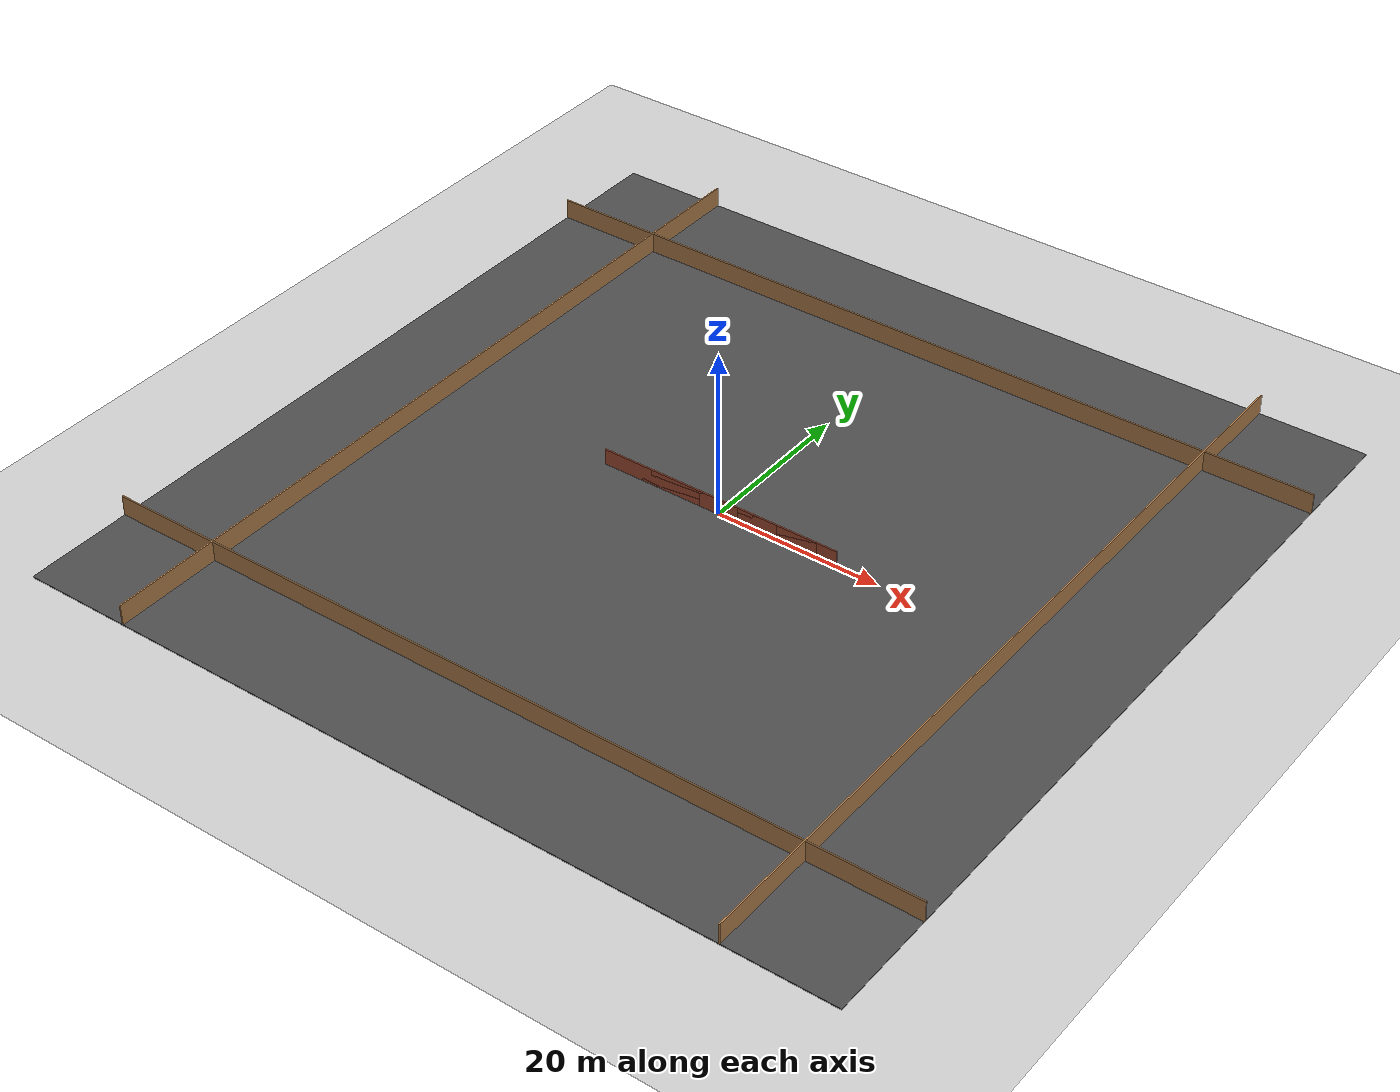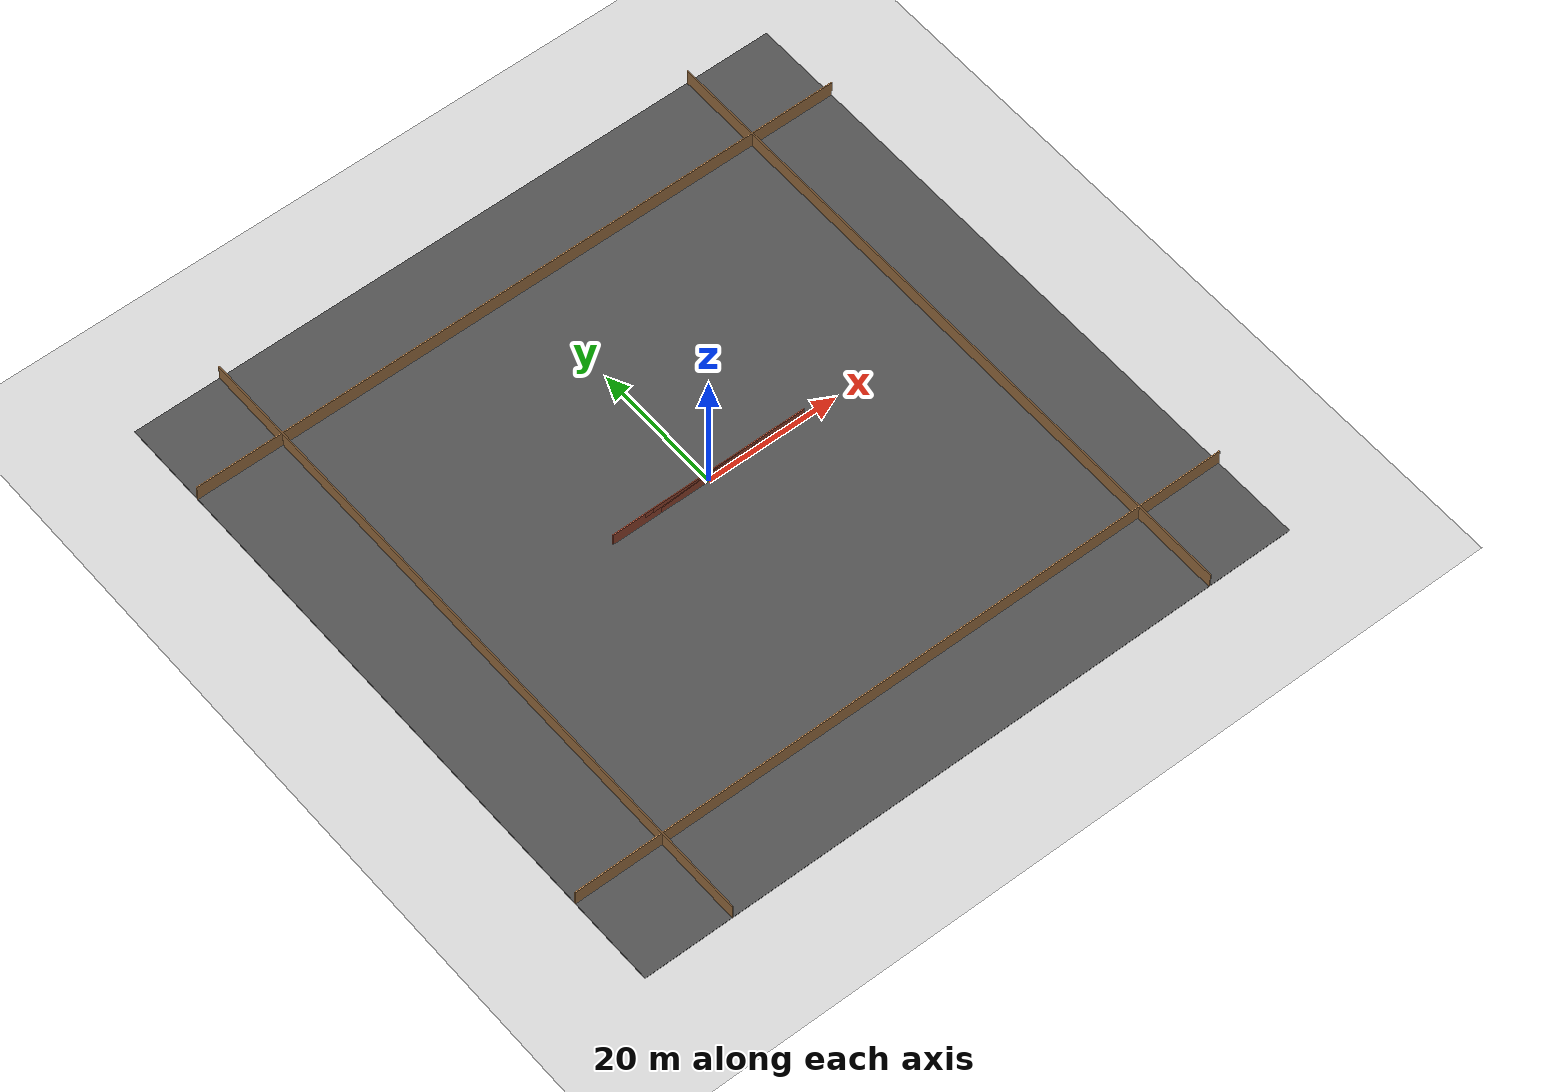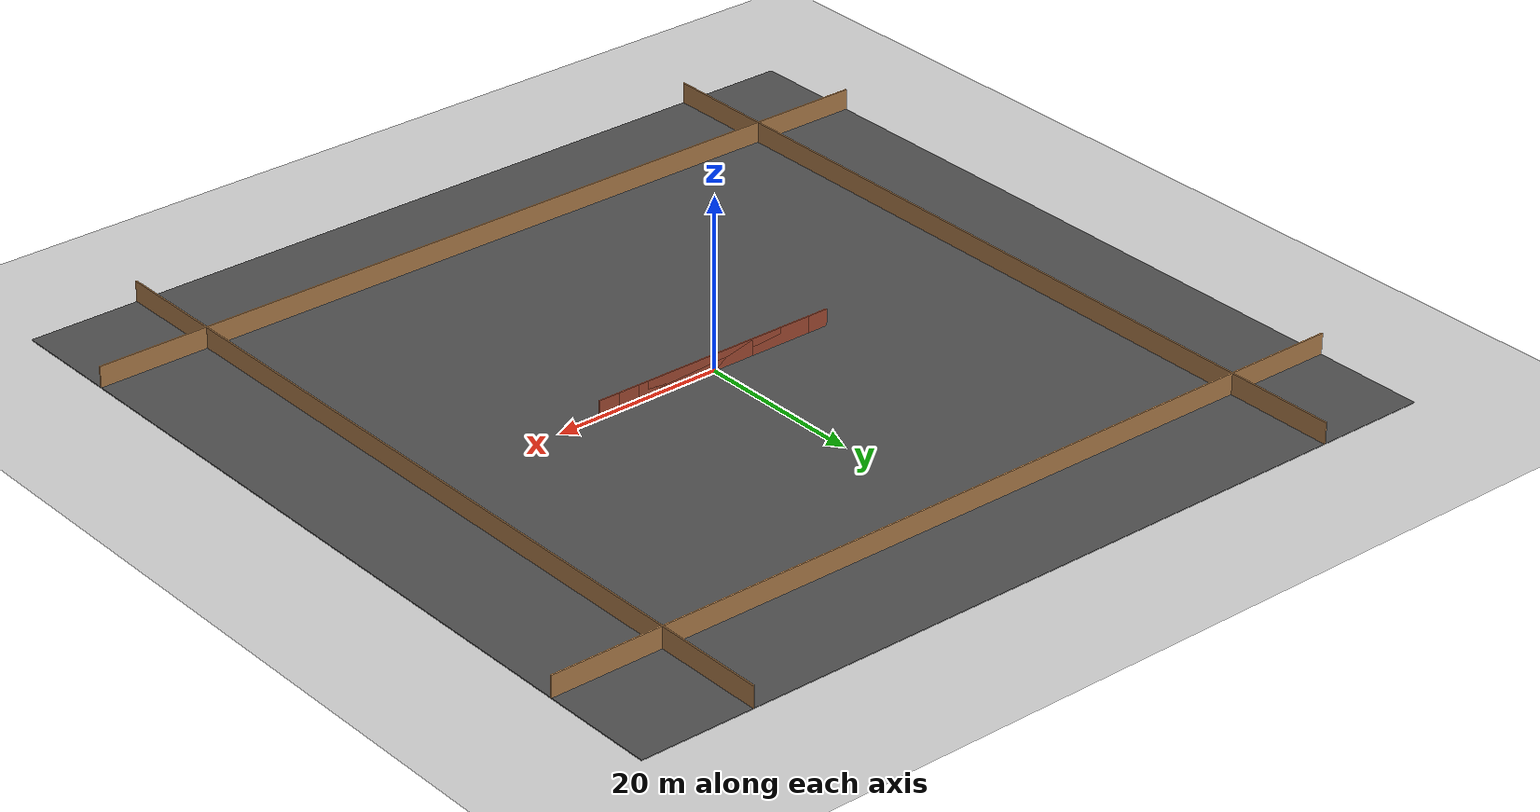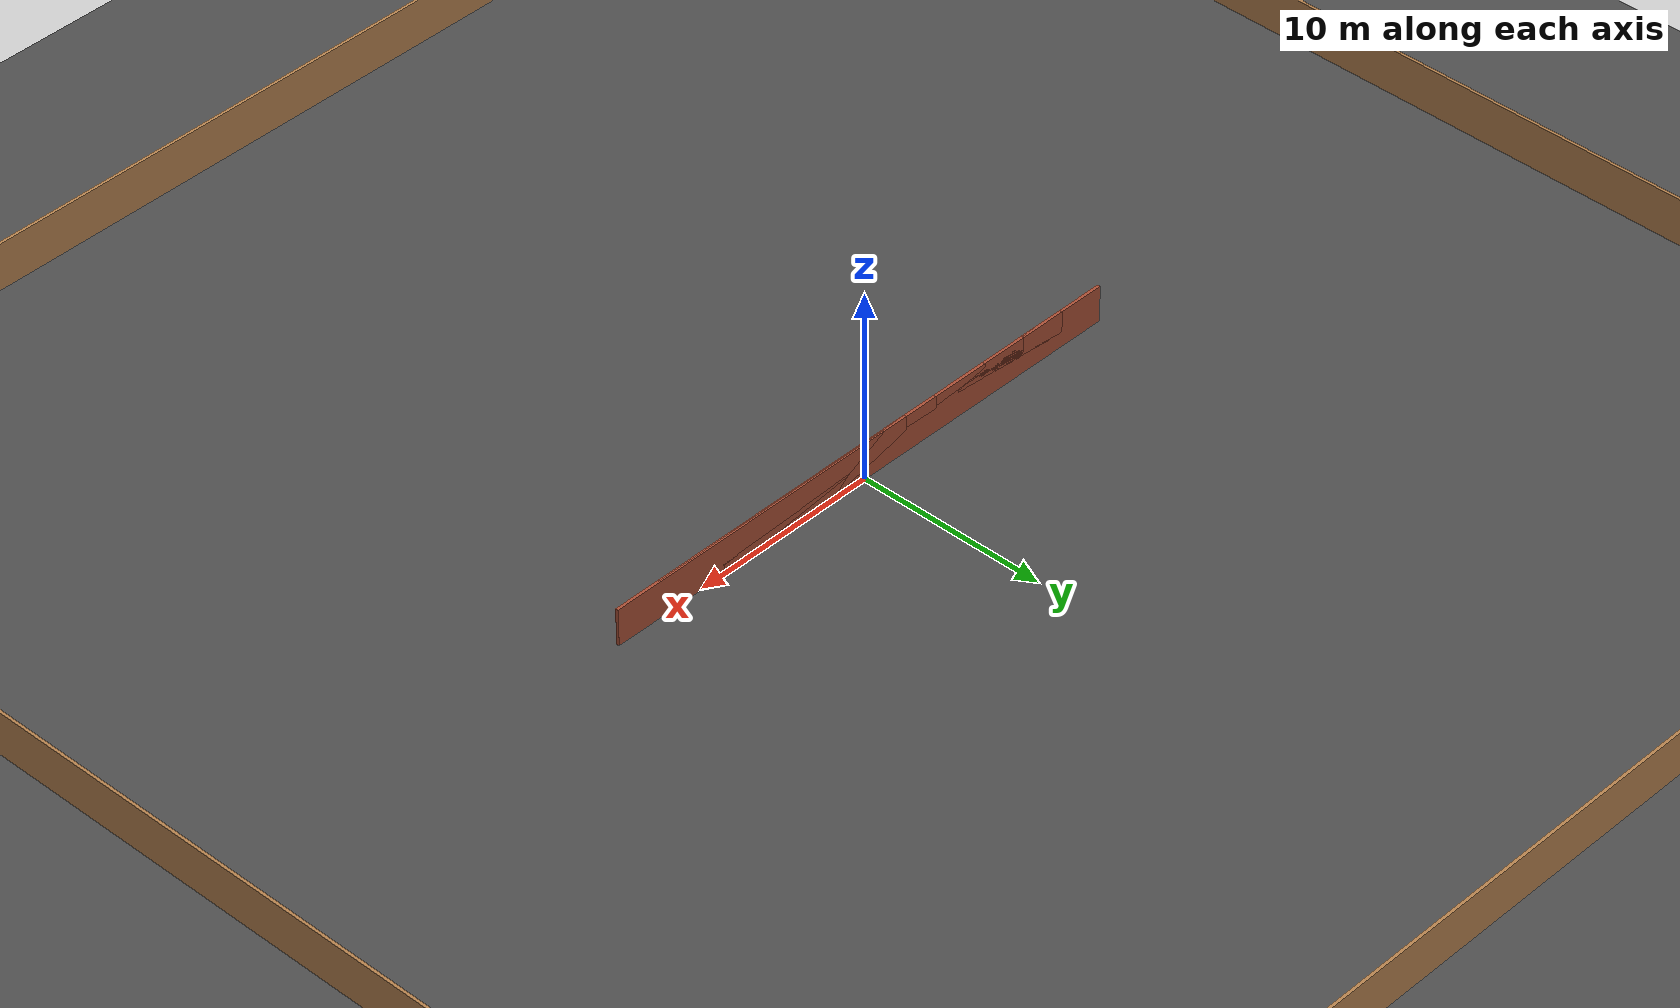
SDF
<sdf version="1.6">
 <world name="default">
  <plugin name="gazebo_connection_plugin" filename="libgazebo_connection_plugin.so"/>
  <light name="sun" type="directional">
   <pose>0 0 10 0 -0 0</pose>
   <diffuse>0.8 0.8 0.8 1</diffuse>
   <specular>0.2 0.2 0.2 1</specular>
   <attenuation>
    <range>1000</range>
    <constant>0.9</constant>
    <linear>0.01</linear>
    <quadratic>0.001</quadratic>
   </attenuation>
   <direction>-0.5 0.1 -0.9</direction>
  </light>
  <model name="ground_plane">
   <static>1</static>
   <link name="link">
    <collision name="collision">
     <geometry><plane><normal>0 0 1</normal><size>100 100</size></plane></geometry>
     <surface><friction><ode><mu>100</mu><mu2>50</mu2></ode></friction></surface>
    </collision>
    <visual name="visual">
     <cast_shadows>0</cast_shadows>
     <geometry><plane><normal>0 0 1</normal><size>100 100</size></plane></geometry>
     <material>
      <script><uri>file://media/materials/scripts/gazebo.material</uri><name>Gazebo/Grey</name></script>
     </material>
    </visual>
   </link>
  </model>
  <gravity>0 0 -9.8</gravity>
  <magnetic_field>6e-06 2.3e-05 -4.2e-05</magnetic_field>
  <atmosphere type="adiabatic"/>
  <physics name="default_physics" default="0" type="ode">
   <max_step_size>0.001</max_step_size>
   <real_time_factor>1</real_time_factor>
   <real_time_update_rate>1000</real_time_update_rate>
  </physics>
  <scene><ambient>0.4 0.4 0.4 1</ambient><background>0.7 0.7 0.7 1</background><shadows>1</shadows></scene>
  <audio><device>default</device></audio>
  <spherical_coordinates>
   <surface_model>EARTH_WGS84</surface_model>
   <latitude_deg>0</latitude_deg>
   <longitude_deg>0</longitude_deg>
   <elevation>0</elevation>
   <heading_deg>0</heading_deg>
  </spherical_coordinates>
  <model name="map_frame">
   <link name="Wall_0">
    <collision name="Wall_0_Collision">
     <geometry><box><size>100.05 0.15 2.5</size></box></geometry>
     <pose>0 0 1.25 0 -0 0</pose>
    </collision>
    <visual name="Wall_0_Visual">
     <pose>0 0 1.25 0 -0 0</pose>
     <geometry><box><size>100.05 0.15 2.5</size></box></geometry>
     <material>
      <script><uri>file://media/materials/scripts/gazebo.material</uri><name>Gazebo/Wood</name></script>
      <ambient>1 1 1 1</ambient>
     </material>
    </visual>
    <pose>0 37 0 0 -0 0</pose>
   </link>
   <link name="Wall_1">
    <collision name="Wall_1_Collision">
     <geometry><box><size>100.05 0.15 2.5</size></box></geometry>
     <pose>0 0 1.25 0 -0 0</pose>
    </collision>
    <visual name="Wall_1_Visual">
     <pose>0 0 1.25 0 -0 0</pose>
     <geometry><box><size>100.05 0.15 2.5</size></box></geometry>
     <material>
      <script><uri>file://media/materials/scripts/gazebo.material</uri><name>Gazebo/Wood</name></script>
      <ambient>1 1 1 1</ambient>
     </material>
    </visual>
    <pose>37 0 0 0 0 -1.5708</pose>
   </link>
   <link name="Wall_2">
    <collision name="Wall_2_Collision">
     <geometry><box><size>100.05 0.15 2.5</size></box></geometry>
     <pose>0 0 1.25 0 -0 0</pose>
    </collision>
    <visual name="Wall_2_Visual">
     <pose>0 0 1.25 0 -0 0</pose>
     <geometry><box><size>100.05 0.15 2.5</size></box></geometry>
     <material>
      <script><uri>file://media/materials/scripts/gazebo.material</uri><name>Gazebo/Wood</name></script>
      <ambient>1 1 1 1</ambient>
     </material>
    </visual>
    <pose>0 -37 0 0 -0 3.14159</pose>
   </link>
   <link name="Wall_3">
    <collision name="Wall_3_Collision">
     <geometry><box><size>100.05 0.15 2.5</size></box></geometry>
     <pose>0 0 1.25 0 -0 0</pose>
    </collision>
    <visual name="Wall_3_Visual">
     <pose>0 0 1.25 0 -0 0</pose>
     <geometry><box><size>100.05 0.15 2.5</size></box></geometry>
     <material>
      <script><uri>file://media/materials/scripts/gazebo.material</uri><name>Gazebo/Wood</name></script>
      <ambient>1 1 1 1</ambient>
     </material>
    </visual>
    <pose>-37 0 0 0 -0 1.5708</pose>
   </link>
   <static>1</static>
  </model>
  <model name="asphalt_plane">
   <static>1</static>
   <link name="link">
    <collision name="collision"><geometry><box><size>100 100 0.1</size></box></geometry></collision>
    <visual name="visual">
     <cast_shadows>0</cast_shadows>
     <geometry><box><size>100 100 0.1</size></box></geometry>
     <material>
      <script>
       <uri>model://asphalt_plane/materials/scripts</uri>
       <uri>model://asphalt_plane/materials/textures</uri>
       <name>vrc/asphalt</name>
      </script>
     </material>
    </visual>
   </link>
  </model>
  <model name="brick_wall_2_8_horizontal">
   <link name="Wall_0">
    <collision name="Wall_0_Collision">
     <geometry><box><size>15.0 0.15 2.0</size></box></geometry>
     <pose>0 0 1.0 0 -0 0</pose>
    </collision>
    <visual name="Wall_0_Visual">
     <pose>0 0 1.0 0 -0 0</pose>
     <geometry><box><size>15.0 0.15 2.0</size></box></geometry>
     <material>
      <script><uri>file://media/materials/scripts/gazebo.material</uri><name>Gazebo/Bricks</name></script>
      <ambient>1 1 1 1</ambient>
     </material>
     <meta><layer>0</layer></meta>
    </visual>
   </link>
   <static>1</static>
  </model>
  <model name="brick_wall_2_16_horizontal">
   <link name="Wall_0">
    <collision name="Wall_0_Collision">
     <geometry><box><size>15.0 0.15 2.0</size></box></geometry>
     <pose>0 0 1.0 0 -0 0</pose>
    </collision>
    <visual name="Wall_0_Visual">
     <pose>0 0 1.0 0 -0 0</pose>
     <geometry><box><size>15.0 0.15 2.0</size></box></geometry>
     <material>
      <script><uri>file://media/materials/scripts/gazebo.material</uri><name>Gazebo/Bricks</name></script>
      <ambient>1 1 1 1</ambient>
     </material>
     <meta><layer>0</layer></meta>
    </visual>
   </link>
   <static>1</static>
  </model>
  <model name="brick_wall_2_26_horizontal">
   <link name="Wall_0">
    <collision name="Wall_0_Collision">
     <geometry><box><size>15.0 0.15 2.0</size></box></geometry>
     <pose>0 0 1.0 0 -0 0</pose>
    </collision>
    <visual name="Wall_0_Visual">
     <pose>0 0 1.0 0 -0 0</pose>
     <geometry><box><size>15.0 0.15 2.0</size></box></geometry>
     <material>
      <script><uri>file://media/materials/scripts/gazebo.material</uri><name>Gazebo/Bricks</name></script>
      <ambient>1 1 1 1</ambient>
     </material>
     <meta><layer>0</layer></meta>
    </visual>
   </link>
   <static>1</static>
  </model>
  <model name="brick_wall_2_32_horizontal">
   <link name="Wall_0">
    <collision name="Wall_0_Collision">
     <geometry><box><size>10.0 0.15 2.0</size></box></geometry>
     <pose>0 0 1.0 0 -0 0</pose>
    </collision>
    <visual name="Wall_0_Visual">
     <pose>0 0 1.0 0 -0 0</pose>
     <geometry><box><size>10.0 0.15 2.0</size></box></geometry>
     <material>
      <script><uri>file://media/materials/scripts/gazebo.material</uri><name>Gazebo/Bricks</name></script>
      <ambient>1 1 1 1</ambient>
     </material>
     <meta><layer>0</layer></meta>
    </visual>
   </link>
   <static>1</static>
  </model>
  <model name="brick_wall_2_36_horizontal">
   <link name="Wall_0">
    <collision name="Wall_0_Collision">
     <geometry><box><size>5.0 0.15 2.0</size></box></geometry>
     <pose>0 0 1.0 0 -0 0</pose>
    </collision>
    <visual name="Wall_0_Visual">
     <pose>0 0 1.0 0 -0 0</pose>
     <geometry><box><size>5.0 0.15 2.0</size></box></geometry>
     <material>
      <script><uri>file://media/materials/scripts/gazebo.material</uri><name>Gazebo/Bricks</name></script>
      <ambient>1 1 1 1</ambient>
     </material>
     <meta><layer>0</layer></meta>
    </visual>
   </link>
   <static>1</static>
  </model>
  <model name="brick_wall_4_8_horizontal">
   <link name="Wall_0">
    <collision name="Wall_0_Collision">
     <geometry><box><size>5.0 0.15 2.0</size></box></geometry>
     <pose>0 0 1.0 0 -0 0</pose>
    </collision>
    <visual name="Wall_0_Visual">
     <pose>0 0 1.0 0 -0 0</pose>
     <geometry><box><size>5.0 0.15 2.0</size></box></geometry>
     <material>
      <script><uri>file://media/materials/scripts/gazebo.material</uri><name>Gazebo/Bricks</name></script>
      <ambient>1 1 1 1</ambient>
     </material>
     <meta><layer>0</layer></meta>
    </visual>
   </link>
   <static>1</static>
  </model>
  <model name="brick_wall_4_14_horizontal">
   <link name="Wall_0">
    <collision name="Wall_0_Collision">
     <geometry><box><size>10.0 0.15 2.0</size></box></geometry>
     <pose>0 0 1.0 0 -0 0</pose>
    </collision>
    <visual name="Wall_0_Visual">
     <pose>0 0 1.0 0 -0 0</pose>
     <geometry><box><size>10.0 0.15 2.0</size></box></geometry>
     <material>
      <script><uri>file://media/materials/scripts/gazebo.material</uri><name>Gazebo/Bricks</name></script>
      <ambient>1 1 1 1</ambient>
     </material>
     <meta><layer>0</layer></meta>
    </visual>
   </link>
   <static>1</static>
  </model>
  <model name="brick_wall_4_18_horizontal">
   <link name="Wall_0">
    <collision name="Wall_0_Collision">
     <geometry><box><size>5.0 0.15 2.0</size></box></geometry>
     <pose>0 0 1.0 0 -0 0</pose>
    </collision>
    <visual name="Wall_0_Visual">
     <pose>0 0 1.0 0 -0 0</pose>
     <geometry><box><size>5.0 0.15 2.0</size></box></geometry>
     <material>
      <script><uri>file://media/materials/scripts/gazebo.material</uri><name>Gazebo/Bricks</name></script>
      <ambient>1 1 1 1</ambient>
     </material>
     <meta><layer>0</layer></meta>
    </visual>
   </link>
   <static>1</static>
  </model>
  <model name="brick_wall_4_22_horizontal">
   <link name="Wall_0">
    <collision name="Wall_0_Collision">
     <geometry><box><size>5.0 0.15 2.0</size></box></geometry>
     <pose>0 0 1.0 0 -0 0</pose>
    </collision>
    <visual name="Wall_0_Visual">
     <pose>0 0 1.0 0 -0 0</pose>
     <geometry><box><size>5.0 0.15 2.0</size></box></geometry>
     <material>
      <script><uri>file://media/materials/scripts/gazebo.material</uri><name>Gazebo/Bricks</name></script>
      <ambient>1 1 1 1</ambient>
     </material>
     <meta><layer>0</layer></meta>
    </visual>
   </link>
   <static>1</static>
  </model>
  <model name="brick_wall_4_28_horizontal">
   <link name="Wall_0">
    <collision name="Wall_0_Collision">
     <geometry><box><size>5.0 0.15 2.0</size></box></geometry>
     <pose>0 0 1.0 0 -0 0</pose>
    </collision>
    <visual name="Wall_0_Visual">
     <pose>0 0 1.0 0 -0 0</pose>
     <geometry><box><size>5.0 0.15 2.0</size></box></geometry>
     <material>
      <script><uri>file://media/materials/scripts/gazebo.material</uri><name>Gazebo/Bricks</name></script>
      <ambient>1 1 1 1</ambient>
     </material>
     <meta><layer>0</layer></meta>
    </visual>
   </link>
   <static>1</static>
  </model>
  <model name="brick_wall_4_38_horizontal">
   <link name="Wall_0">
    <collision name="Wall_0_Collision">
     <geometry><box><size>5.0 0.15 2.0</size></box></geometry>
     <pose>0 0 1.0 0 -0 0</pose>
    </collision>
    <visual name="Wall_0_Visual">
     <pose>0 0 1.0 0 -0 0</pose>
     <geometry><box><size>5.0 0.15 2.0</size></box></geometry>
     <material>
      <script><uri>file://media/materials/scripts/gazebo.material</uri><name>Gazebo/Bricks</name></script>
      <ambient>1 1 1 1</ambient>
     </material>
     <meta><layer>0</layer></meta>
    </visual>
   </link>
   <static>1</static>
  </model>
  <model name="brick_wall_6_6_horizontal">
   <link name="Wall_0">
    <collision name="Wall_0_Collision">
     <geometry><box><size>5.0 0.15 2.0</size></box></geometry>
     <pose>0 0 1.0 0 -0 0</pose>
    </collision>
    <visual name="Wall_0_Visual">
     <pose>0 0 1.0 0 -0 0</pose>
     <geometry><box><size>5.0 0.15 2.0</size></box></geometry>
     <material>
      <script><uri>file://media/materials/scripts/gazebo.material</uri><name>Gazebo/Bricks</name></script>
      <ambient>1 1 1 1</ambient>
     </material>
     <meta><layer>0</layer></meta>
    </visual>
   </link>
   <static>1</static>
  </model>
  <model name="brick_wall_6_10_horizontal">
   <link name="Wall_0">
    <collision name="Wall_0_Collision">
     <geometry><box><size>5.0 0.15 2.0</size></box></geometry>
     <pose>0 0 1.0 0 -0 0</pose>
    </collision>
    <visual name="Wall_0_Visual">
     <pose>0 0 1.0 0 -0 0</pose>
     <geometry><box><size>5.0 0.15 2.0</size></box></geometry>
     <material>
      <script><uri>file://media/materials/scripts/gazebo.material</uri><name>Gazebo/Bricks</name></script>
      <ambient>1 1 1 1</ambient>
     </material>
     <meta><layer>0</layer></meta>
    </visual>
   </link>
   <static>1</static>
  </model>
  <model name="brick_wall_6_14_horizontal">
   <link name="Wall_0">
    <collision name="Wall_0_Collision">
     <geometry><box><size>5.0 0.15 2.0</size></box></geometry>
     <pose>0 0 1.0 0 -0 0</pose>
    </collision>
    <visual name="Wall_0_Visual">
     <pose>0 0 1.0 0 -0 0</pose>
     <geometry><box><size>5.0 0.15 2.0</size></box></geometry>
     <material>
      <script><uri>file://media/materials/scripts/gazebo.material</uri><name>Gazebo/Bricks</name></script>
      <ambient>1 1 1 1</ambient>
     </material>
     <meta><layer>0</layer></meta>
    </visual>
   </link>
   <static>1</static>
  </model>
  <model name="brick_wall_6_18_horizontal">
   <link name="Wall_0">
    <collision name="Wall_0_Collision">
     <geometry><box><size>5.0 0.15 2.0</size></box></geometry>
     <pose>0 0 1.0 0 -0 0</pose>
    </collision>
    <visual name="Wall_0_Visual">
     <pose>0 0 1.0 0 -0 0</pose>
     <geometry><box><size>5.0 0.15 2.0</size></box></geometry>
     <material>
      <script><uri>file://media/materials/scripts/gazebo.material</uri><name>Gazebo/Bricks</name></script>
      <ambient>1 1 1 1</ambient>
     </material>
     <meta><layer>0</layer></meta>
    </visual>
   </link>
   <static>1</static>
  </model>
  <model name="brick_wall_6_24_horizontal">
   <link name="Wall_0">
    <collision name="Wall_0_Collision">
     <geometry><box><size>5.0 0.15 2.0</size></box></geometry>
     <pose>0 0 1.0 0 -0 0</pose>
    </collision>
    <visual name="Wall_0_Visual">
     <pose>0 0 1.0 0 -0 0</pose>
     <geometry><box><size>5.0 0.15 2.0</size></box></geometry>
     <material>
      <script><uri>file://media/materials/scripts/gazebo.material</uri><name>Gazebo/Bricks</name></script>
      <ambient>1 1 1 1</ambient>
     </material>
     <meta><layer>0</layer></meta>
    </visual>
   </link>
   <static>1</static>
  </model>
  <model name="brick_wall_6_32_horizontal">
   <link name="Wall_0">
    <collision name="Wall_0_Collision">
     <geometry><box><size>5.0 0.15 2.0</size></box></geometry>
     <pose>0 0 1.0 0 -0 0</pose>
    </collision>
    <visual name="Wall_0_Visual">
     <pose>0 0 1.0 0 -0 0</pose>
     <geometry><box><size>5.0 0.15 2.0</size></box></geometry>
     <material>
      <script><uri>file://media/materials/scripts/gazebo.material</uri><name>Gazebo/Bricks</name></script>
      <ambient>1 1 1 1</ambient>
     </material>
     <meta><layer>0</layer></meta>
    </visual>
   </link>
   <static>1</static>
  </model>
  <model name="brick_wall_6_38_horizontal">
   <link name="Wall_0">
    <collision name="Wall_0_Collision">
     <geometry><box><size>10.0 0.15 2.0</size></box></geometry>
     <pose>0 0 1.0 0 -0 0</pose>
    </collision>
    <visual name="Wall_0_Visual">
     <pose>0 0 1.0 0 -0 0</pose>
     <geometry><box><size>10.0 0.15 2.0</size></box></geometry>
     <material>
      <script><uri>file://media/materials/scripts/gazebo.material</uri><name>Gazebo/Bricks</name></script>
      <ambient>1 1 1 1</ambient>
     </material>
     <meta><layer>0</layer></meta>
    </visual>
   </link>
   <static>1</static>
  </model>
  <model name="brick_wall_8_8_horizontal">
   <link name="Wall_0">
    <collision name="Wall_0_Collision">
     <geometry><box><size>5.0 0.15 2.0</size></box></geometry>
     <pose>0 0 1.0 0 -0 0</pose>
    </collision>
    <visual name="Wall_0_Visual">
     <pose>0 0 1.0 0 -0 0</pose>
     <geometry><box><size>5.0 0.15 2.0</size></box></geometry>
     <material>
      <script><uri>file://media/materials/scripts/gazebo.material</uri><name>Gazebo/Bricks</name></script>
      <ambient>1 1 1 1</ambient>
     </material>
     <meta><layer>0</layer></meta>
    </visual>
   </link>
   <static>1</static>
  </model>
  <model name="brick_wall_8_12_horizontal">
   <link name="Wall_0">
    <collision name="Wall_0_Collision">
     <geometry><box><size>5.0 0.15 2.0</size></box></geometry>
     <pose>0 0 1.0 0 -0 0</pose>
    </collision>
    <visual name="Wall_0_Visual">
     <pose>0 0 1.0 0 -0 0</pose>
     <geometry><box><size>5.0 0.15 2.0</size></box></geometry>
     <material>
      <script><uri>file://media/materials/scripts/gazebo.material</uri><name>Gazebo/Bricks</name></script>
      <ambient>1 1 1 1</ambient>
     </material>
     <meta><layer>0</layer></meta>
    </visual>
   </link>
   <static>1</static>
  </model>
  <model name="brick_wall_8_22_horizontal">
   <link name="Wall_0">
    <collision name="Wall_0_Collision">
     <geometry><box><size>5.0 0.15 2.0</size></box></geometry>
     <pose>0 0 1.0 0 -0 0</pose>
    </collision>
    <visual name="Wall_0_Visual">
     <pose>0 0 1.0 0 -0 0</pose>
     <geometry><box><size>5.0 0.15 2.0</size></box></geometry>
     <material>
      <script><uri>file://media/materials/scripts/gazebo.material</uri><name>Gazebo/Bricks</name></script>
      <ambient>1 1 1 1</ambient>
     </material>
     <meta><layer>0</layer></meta>
    </visual>
   </link>
   <static>1</static>
  </model>
  <model name="brick_wall_8_32_horizontal">
   <link name="Wall_0">
    <collision name="Wall_0_Collision">
     <geometry><box><size>10.0 0.15 2.0</size></box></geometry>
     <pose>0 0 1.0 0 -0 0</pose>
    </collision>
    <visual name="Wall_0_Visual">
     <pose>0 0 1.0 0 -0 0</pose>
     <geometry><box><size>10.0 0.15 2.0</size></box></geometry>
     <material>
      <script><uri>file://media/materials/scripts/gazebo.material</uri><name>Gazebo/Bricks</name></script>
      <ambient>1 1 1 1</ambient>
     </material>
     <meta><layer>0</layer></meta>
    </visual>
   </link>
   <static>1</static>
  </model>
  <model name="brick_wall_8_36_horizontal">
   <link name="Wall_0">
    <collision name="Wall_0_Collision">
     <geometry><box><size>5.0 0.15 2.0</size></box></geometry>
     <pose>0 0 1.0 0 -0 0</pose>
    </collision>
    <visual name="Wall_0_Visual">
     <pose>0 0 1.0 0 -0 0</pose>
     <geometry><box><size>5.0 0.15 2.0</size></box></geometry>
     <material>
      <script><uri>file://media/materials/scripts/gazebo.material</uri><name>Gazebo/Bricks</name></script>
      <ambient>1 1 1 1</ambient>
     </material>
     <meta><layer>0</layer></meta>
    </visual>
   </link>
   <static>1</static>
  </model>
  <model name="brick_wall_10_6_horizontal">
   <link name="Wall_0">
    <collision name="Wall_0_Collision">
     <geometry><box><size>5.0 0.15 2.0</size></box></geometry>
     <pose>0 0 1.0 0 -0 0</pose>
    </collision>
    <visual name="Wall_0_Visual">
     <pose>0 0 1.0 0 -0 0</pose>
     <geometry><box><size>5.0 0.15 2.0</size></box></geometry>
     <material>
      <script><uri>file://media/materials/scripts/gazebo.material</uri><name>Gazebo/Bricks</name></script>
      <ambient>1 1 1 1</ambient>
     </material>
     <meta><layer>0</layer></meta>
    </visual>
   </link>
   <static>1</static>
  </model>
  <model name="brick_wall_10_16_horizontal">
   <link name="Wall_0">
    <collision name="Wall_0_Collision">
     <geometry><box><size>15.0 0.15 2.0</size></box></geometry>
     <pose>0 0 1.0 0 -0 0</pose>
    </collision>
    <visual name="Wall_0_Visual">
     <pose>0 0 1.0 0 -0 0</pose>
     <geometry><box><size>15.0 0.15 2.0</size></box></geometry>
     <material>
      <script><uri>file://media/materials/scripts/gazebo.material</uri><name>Gazebo/Bricks</name></script>
      <ambient>1 1 1 1</ambient>
     </material>
     <meta><layer>0</layer></meta>
    </visual>
   </link>
   <static>1</static>
  </model>
  <model name="brick_wall_10_24_horizontal">
   <link name="Wall_0">
    <collision name="Wall_0_Collision">
     <geometry><box><size>15.0 0.15 2.0</size></box></geometry>
     <pose>0 0 1.0 0 -0 0</pose>
    </collision>
    <visual name="Wall_0_Visual">
     <pose>0 0 1.0 0 -0 0</pose>
     <geometry><box><size>15.0 0.15 2.0</size></box></geometry>
     <material>
      <script><uri>file://media/materials/scripts/gazebo.material</uri><name>Gazebo/Bricks</name></script>
      <ambient>1 1 1 1</ambient>
     </material>
     <meta><layer>0</layer></meta>
    </visual>
   </link>
   <static>1</static>
  </model>
  <model name="brick_wall_10_30_horizontal">
   <link name="Wall_0">
    <collision name="Wall_0_Collision">
     <geometry><box><size>10.0 0.15 2.0</size></box></geometry>
     <pose>0 0 1.0 0 -0 0</pose>
    </collision>
    <visual name="Wall_0_Visual">
     <pose>0 0 1.0 0 -0 0</pose>
     <geometry><box><size>10.0 0.15 2.0</size></box></geometry>
     <material>
      <script><uri>file://media/materials/scripts/gazebo.material</uri><name>Gazebo/Bricks</name></script>
      <ambient>1 1 1 1</ambient>
     </material>
     <meta><layer>0</layer></meta>
    </visual>
   </link>
   <static>1</static>
  </model>
  <model name="brick_wall_12_10_horizontal">
   <link name="Wall_0">
    <collision name="Wall_0_Collision">
     <geometry><box><size>15.0 0.15 2.0</size></box></geometry>
     <pose>0 0 1.0 0 -0 0</pose>
    </collision>
    <visual name="Wall_0_Visual">
     <pose>0 0 1.0 0 -0 0</pose>
     <geometry><box><size>15.0 0.15 2.0</size></box></geometry>
     <material>
      <script><uri>file://media/materials/scripts/gazebo.material</uri><name>Gazebo/Bricks</name></script>
      <ambient>1 1 1 1</ambient>
     </material>
     <meta><layer>0</layer></meta>
    </visual>
   </link>
   <static>1</static>
  </model>
  <model name="brick_wall_12_18_horizontal">
   <link name="Wall_0">
    <collision name="Wall_0_Collision">
     <geometry><box><size>15.0 0.15 2.0</size></box></geometry>
     <pose>0 0 1.0 0 -0 0</pose>
    </collision>
    <visual name="Wall_0_Visual">
     <pose>0 0 1.0 0 -0 0</pose>
     <geometry><box><size>15.0 0.15 2.0</size></box></geometry>
     <material>
      <script><uri>file://media/materials/scripts/gazebo.material</uri><name>Gazebo/Bricks</name></script>
      <ambient>1 1 1 1</ambient>
     </material>
     <meta><layer>0</layer></meta>
    </visual>
   </link>
   <static>1</static>
  </model>
  <model name="brick_wall_12_26_horizontal">
   <link name="Wall_0">
    <collision name="Wall_0_Collision">
     <geometry><box><size>10.0 0.15 2.0</size></box></geometry>
     <pose>0 0 1.0 0 -0 0</pose>
    </collision>
    <visual name="Wall_0_Visual">
     <pose>0 0 1.0 0 -0 0</pose>
     <geometry><box><size>10.0 0.15 2.0</size></box></geometry>
     <material>
      <script><uri>file://media/materials/scripts/gazebo.material</uri><name>Gazebo/Bricks</name></script>
      <ambient>1 1 1 1</ambient>
     </material>
     <meta><layer>0</layer></meta>
    </visual>
   </link>
   <static>1</static>
  </model>
  <model name="brick_wall_12_36_horizontal">
   <link name="Wall_0">
    <collision name="Wall_0_Collision">
     <geometry><box><size>5.0 0.15 2.0</size></box></geometry>
     <pose>0 0 1.0 0 -0 0</pose>
    </collision>
    <visual name="Wall_0_Visual">
     <pose>0 0 1.0 0 -0 0</pose>
     <geometry><box><size>5.0 0.15 2.0</size></box></geometry>
     <material>
      <script><uri>file://media/materials/scripts/gazebo.material</uri><name>Gazebo/Bricks</name></script>
      <ambient>1 1 1 1</ambient>
     </material>
     <meta><layer>0</layer></meta>
    </visual>
   </link>
   <static>1</static>
  </model>
  <model name="brick_wall_14_6_horizontal">
   <link name="Wall_0">
    <collision name="Wall_0_Collision">
     <geometry><box><size>10.0 0.15 2.0</size></box></geometry>
     <pose>0 0 1.0 0 -0 0</pose>
    </collision>
    <visual name="Wall_0_Visual">
     <pose>0 0 1.0 0 -0 0</pose>
     <geometry><box><size>10.0 0.15 2.0</size></box></geometry>
     <material>
      <script><uri>file://media/materials/scripts/gazebo.material</uri><name>Gazebo/Bricks</name></script>
      <ambient>1 1 1 1</ambient>
     </material>
     <meta><layer>0</layer></meta>
    </visual>
   </link>
   <static>1</static>
  </model>
  <model name="brick_wall_14_12_horizontal">
   <link name="Wall_0">
    <collision name="Wall_0_Collision">
     <geometry><box><size>10.0 0.15 2.0</size></box></geometry>
     <pose>0 0 1.0 0 -0 0</pose>
    </collision>
    <visual name="Wall_0_Visual">
     <pose>0 0 1.0 0 -0 0</pose>
     <geometry><box><size>10.0 0.15 2.0</size></box></geometry>
     <material>
      <script><uri>file://media/materials/scripts/gazebo.material</uri><name>Gazebo/Bricks</name></script>
      <ambient>1 1 1 1</ambient>
     </material>
     <meta><layer>0</layer></meta>
    </visual>
   </link>
   <static>1</static>
  </model>
  <model name="brick_wall_14_18_horizontal">
   <link name="Wall_0">
    <collision name="Wall_0_Collision">
     <geometry><box><size>10.0 0.15 2.0</size></box></geometry>
     <pose>0 0 1.0 0 -0 0</pose>
    </collision>
    <visual name="Wall_0_Visual">
     <pose>0 0 1.0 0 -0 0</pose>
     <geometry><box><size>10.0 0.15 2.0</size></box></geometry>
     <material>
      <script><uri>file://media/materials/scripts/gazebo.material</uri><name>Gazebo/Bricks</name></script>
      <ambient>1 1 1 1</ambient>
     </material>
     <meta><layer>0</layer></meta>
    </visual>
   </link>
   <static>1</static>
  </model>
  <model name="brick_wall_14_24_horizontal">
   <link name="Wall_0">
    <collision name="Wall_0_Collision">
     <geometry><box><size>5.0 0.15 2.0</size></box></geometry>
     <pose>0 0 1.0 0 -0 0</pose>
    </collision>
    <visual name="Wall_0_Visual">
     <pose>0 0 1.0 0 -0 0</pose>
     <geometry><box><size>5.0 0.15 2.0</size></box></geometry>
     <material>
      <script><uri>file://media/materials/scripts/gazebo.material</uri><name>Gazebo/Bricks</name></script>
      <ambient>1 1 1 1</ambient>
     </material>
     <meta><layer>0</layer></meta>
    </visual>
   </link>
   <static>1</static>
  </model>
  <model name="brick_wall_14_36_horizontal">
   <link name="Wall_0">
    <collision name="Wall_0_Collision">
     <geometry><box><size>15.0 0.15 2.0</size></box></geometry>
     <pose>0 0 1.0 0 -0 0</pose>
    </collision>
    <visual name="Wall_0_Visual">
     <pose>0 0 1.0 0 -0 0</pose>
     <geometry><box><size>15.0 0.15 2.0</size></box></geometry>
     <material>
      <script><uri>file://media/materials/scripts/gazebo.material</uri><name>Gazebo/Bricks</name></script>
      <ambient>1 1 1 1</ambient>
     </material>
     <meta><layer>0</layer></meta>
    </visual>
   </link>
   <static>1</static>
  </model>
  <model name="brick_wall_16_6_horizontal">
   <link name="Wall_0">
    <collision name="Wall_0_Collision">
     <geometry><box><size>10.0 0.15 2.0</size></box></geometry>
     <pose>0 0 1.0 0 -0 0</pose>
    </collision>
    <visual name="Wall_0_Visual">
     <pose>0 0 1.0 0 -0 0</pose>
     <geometry><box><size>10.0 0.15 2.0</size></box></geometry>
     <material>
      <script><uri>file://media/materials/scripts/gazebo.material</uri><name>Gazebo/Bricks</name></script>
      <ambient>1 1 1 1</ambient>
     </material>
     <meta><layer>0</layer></meta>
    </visual>
   </link>
   <static>1</static>
  </model>
  <model name="brick_wall_16_12_horizontal">
   <link name="Wall_0">
    <collision name="Wall_0_Collision">
     <geometry><box><size>10.0 0.15 2.0</size></box></geometry>
     <pose>0 0 1.0 0 -0 0</pose>
    </collision>
    <visual name="Wall_0_Visual">
     <pose>0 0 1.0 0 -0 0</pose>
     <geometry><box><size>10.0 0.15 2.0</size></box></geometry>
     <material>
      <script><uri>file://media/materials/scripts/gazebo.material</uri><name>Gazebo/Bricks</name></script>
      <ambient>1 1 1 1</ambient>
     </material>
     <meta><layer>0</layer></meta>
    </visual>
   </link>
   <static>1</static>
  </model>
  <model name="brick_wall_16_24_horizontal">
   <link name="Wall_0">
    <collision name="Wall_0_Collision">
     <geometry><box><size>25.0 0.15 2.0</size></box></geometry>
     <pose>0 0 1.0 0 -0 0</pose>
    </collision>
    <visual name="Wall_0_Visual">
     <pose>0 0 1.0 0 -0 0</pose>
     <geometry><box><size>25.0 0.15 2.0</size></box></geometry>
     <material>
      <script><uri>file://media/materials/scripts/gazebo.material</uri><name>Gazebo/Bricks</name></script>
      <ambient>1 1 1 1</ambient>
     </material>
     <meta><layer>0</layer></meta>
    </visual>
   </link>
   <static>1</static>
  </model>
  <model name="brick_wall_16_28_horizontal">
   <link name="Wall_0">
    <collision name="Wall_0_Collision">
     <geometry><box><size>5.0 0.15 2.0</size></box></geometry>
     <pose>0 0 1.0 0 -0 0</pose>
    </collision>
    <visual name="Wall_0_Visual">
     <pose>0 0 1.0 0 -0 0</pose>
     <geometry><box><size>5.0 0.15 2.0</size></box></geometry>
     <material>
      <script><uri>file://media/materials/scripts/gazebo.material</uri><name>Gazebo/Bricks</name></script>
      <ambient>1 1 1 1</ambient>
     </material>
     <meta><layer>0</layer></meta>
    </visual>
   </link>
   <static>1</static>
  </model>
  <model name="brick_wall_16_32_horizontal">
   <link name="Wall_0">
    <collision name="Wall_0_Collision">
     <geometry><box><size>5.0 0.15 2.0</size></box></geometry>
     <pose>0 0 1.0 0 -0 0</pose>
    </collision>
    <visual name="Wall_0_Visual">
     <pose>0 0 1.0 0 -0 0</pose>
     <geometry><box><size>5.0 0.15 2.0</size></box></geometry>
     <material>
      <script><uri>file://media/materials/scripts/gazebo.material</uri><name>Gazebo/Bricks</name></script>
      <ambient>1 1 1 1</ambient>
     </material>
     <meta><layer>0</layer></meta>
    </visual>
   </link>
   <static>1</static>
  </model>
  <model name="brick_wall_16_38_horizontal">
   <link name="Wall_0">
    <collision name="Wall_0_Collision">
     <geometry><box><size>5.0 0.15 2.0</size></box></geometry>
     <pose>0 0 1.0 0 -0 0</pose>
    </collision>
    <visual name="Wall_0_Visual">
     <pose>0 0 1.0 0 -0 0</pose>
     <geometry><box><size>5.0 0.15 2.0</size></box></geometry>
     <material>
      <script><uri>file://media/materials/scripts/gazebo.material</uri><name>Gazebo/Bricks</name></script>
      <ambient>1 1 1 1</ambient>
     </material>
     <meta><layer>0</layer></meta>
    </visual>
   </link>
   <static>1</static>
  </model>
  <model name="brick_wall_18_6_horizontal">
   <link name="Wall_0">
    <collision name="Wall_0_Collision">
     <geometry><box><size>5.0 0.15 2.0</size></box></geometry>
     <pose>0 0 1.0 0 -0 0</pose>
    </collision>
    <visual name="Wall_0_Visual">
     <pose>0 0 1.0 0 -0 0</pose>
     <geometry><box><size>5.0 0.15 2.0</size></box></geometry>
     <material>
      <script><uri>file://media/materials/scripts/gazebo.material</uri><name>Gazebo/Bricks</name></script>
      <ambient>1 1 1 1</ambient>
     </material>
     <meta><layer>0</layer></meta>
    </visual>
   </link>
   <static>1</static>
  </model>
  <model name="brick_wall_18_16_horizontal">
   <link name="Wall_0">
    <collision name="Wall_0_Collision">
     <geometry><box><size>5.0 0.15 2.0</size></box></geometry>
     <pose>0 0 1.0 0 -0 0</pose>
    </collision>
    <visual name="Wall_0_Visual">
     <pose>0 0 1.0 0 -0 0</pose>
     <geometry><box><size>5.0 0.15 2.0</size></box></geometry>
     <material>
      <script><uri>file://media/materials/scripts/gazebo.material</uri><name>Gazebo/Bricks</name></script>
      <ambient>1 1 1 1</ambient>
     </material>
     <meta><layer>0</layer></meta>
    </visual>
   </link>
   <static>1</static>
  </model>
  <model name="brick_wall_18_22_horizontal">
   <link name="Wall_0">
    <collision name="Wall_0_Collision">
     <geometry><box><size>10.0 0.15 2.0</size></box></geometry>
     <pose>0 0 1.0 0 -0 0</pose>
    </collision>
    <visual name="Wall_0_Visual">
     <pose>0 0 1.0 0 -0 0</pose>
     <geometry><box><size>10.0 0.15 2.0</size></box></geometry>
     <material>
      <script><uri>file://media/materials/scripts/gazebo.material</uri><name>Gazebo/Bricks</name></script>
      <ambient>1 1 1 1</ambient>
     </material>
     <meta><layer>0</layer></meta>
    </visual>
   </link>
   <static>1</static>
  </model>
  <model name="brick_wall_18_28_horizontal">
   <link name="Wall_0">
    <collision name="Wall_0_Collision">
     <geometry><box><size>10.0 0.15 2.0</size></box></geometry>
     <pose>0 0 1.0 0 -0 0</pose>
    </collision>
    <visual name="Wall_0_Visual">
     <pose>0 0 1.0 0 -0 0</pose>
     <geometry><box><size>10.0 0.15 2.0</size></box></geometry>
     <material>
      <script><uri>file://media/materials/scripts/gazebo.material</uri><name>Gazebo/Bricks</name></script>
      <ambient>1 1 1 1</ambient>
     </material>
     <meta><layer>0</layer></meta>
    </visual>
   </link>
   <static>1</static>
  </model>
  <model name="brick_wall_18_32_horizontal">
   <link name="Wall_0">
    <collision name="Wall_0_Collision">
     <geometry><box><size>5.0 0.15 2.0</size></box></geometry>
     <pose>0 0 1.0 0 -0 0</pose>
    </collision>
    <visual name="Wall_0_Visual">
     <pose>0 0 1.0 0 -0 0</pose>
     <geometry><box><size>5.0 0.15 2.0</size></box></geometry>
     <material>
      <script><uri>file://media/materials/scripts/gazebo.material</uri><name>Gazebo/Bricks</name></script>
      <ambient>1 1 1 1</ambient>
     </material>
     <meta><layer>0</layer></meta>
    </visual>
   </link>
   <static>1</static>
  </model>
  <model name="brick_wall_18_38_horizontal">
   <link name="Wall_0">
    <collision name="Wall_0_Collision">
     <geometry><box><size>5.0 0.15 2.0</size></box></geometry>
     <pose>0 0 1.0 0 -0 0</pose>
    </collision>
    <visual name="Wall_0_Visual">
     <pose>0 0 1.0 0 -0 0</pose>
     <geometry><box><size>5.0 0.15 2.0</size></box></geometry>
     <material>
      <script><uri>file://media/materials/scripts/gazebo.material</uri><name>Gazebo/Bricks</name></script>
      <ambient>1 1 1 1</ambient>
     </material>
     <meta><layer>0</layer></meta>
    </visual>
   </link>
   <static>1</static>
  </model>
  <model name="brick_wall_20_4_horizontal">
   <link name="Wall_0">
    <collision name="Wall_0_Collision">
     <geometry><box><size>5.0 0.15 2.0</size></box></geometry>
     <pose>0 0 1.0 0 -0 0</pose>
    </collision>
    <visual name="Wall_0_Visual">
     <pose>0 0 1.0 0 -0 0</pose>
     <geometry><box><size>5.0 0.15 2.0</size></box></geometry>
     <material>
      <script><uri>file://media/materials/scripts/gazebo.material</uri><name>Gazebo/Bricks</name></script>
      <ambient>1 1 1 1</ambient>
     </material>
     <meta><layer>0</layer></meta>
    </visual>
   </link>
   <static>1</static>
  </model>
  <model name="brick_wall_20_10_horizontal">
   <link name="Wall_0">
    <collision name="Wall_0_Collision">
     <geometry><box><size>5.0 0.15 2.0</size></box></geometry>
     <pose>0 0 1.0 0 -0 0</pose>
    </collision>
    <visual name="Wall_0_Visual">
     <pose>0 0 1.0 0 -0 0</pose>
     <geometry><box><size>5.0 0.15 2.0</size></box></geometry>
     <material>
      <script><uri>file://media/materials/scripts/gazebo.material</uri><name>Gazebo/Bricks</name></script>
      <ambient>1 1 1 1</ambient>
     </material>
     <meta><layer>0</layer></meta>
    </visual>
   </link>
   <static>1</static>
  </model>
  <model name="brick_wall_20_18_horizontal">
   <link name="Wall_0">
    <collision name="Wall_0_Collision">
     <geometry><box><size>15.0 0.15 2.0</size></box></geometry>
     <pose>0 0 1.0 0 -0 0</pose>
    </collision>
    <visual name="Wall_0_Visual">
     <pose>0 0 1.0 0 -0 0</pose>
     <geometry><box><size>15.0 0.15 2.0</size></box></geometry>
     <material>
      <script><uri>file://media/materials/scripts/gazebo.material</uri><name>Gazebo/Bricks</name></script>
      <ambient>1 1 1 1</ambient>
     </material>
     <meta><layer>0</layer></meta>
    </visual>
   </link>
   <static>1</static>
  </model>
  <model name="brick_wall_20_26_horizontal">
   <link name="Wall_0">
    <collision name="Wall_0_Collision">
     <geometry><box><size>5.0 0.15 2.0</size></box></geometry>
     <pose>0 0 1.0 0 -0 0</pose>
    </collision>
    <visual name="Wall_0_Visual">
     <pose>0 0 1.0 0 -0 0</pose>
     <geometry><box><size>5.0 0.15 2.0</size></box></geometry>
     <material>
      <script><uri>file://media/materials/scripts/gazebo.material</uri><name>Gazebo/Bricks</name></script>
      <ambient>1 1 1 1</ambient>
     </material>
     <meta><layer>0</layer></meta>
    </visual>
   </link>
   <static>1</static>
  </model>
  <model name="brick_wall_20_32_horizontal">
   <link name="Wall_0">
    <collision name="Wall_0_Collision">
     <geometry><box><size>10.0 0.15 2.0</size></box></geometry>
     <pose>0 0 1.0 0 -0 0</pose>
    </collision>
    <visual name="Wall_0_Visual">
     <pose>0 0 1.0 0 -0 0</pose>
     <geometry><box><size>10.0 0.15 2.0</size></box></geometry>
     <material>
      <script><uri>file://media/materials/scripts/gazebo.material</uri><name>Gazebo/Bricks</name></script>
      <ambient>1 1 1 1</ambient>
     </material>
     <meta><layer>0</layer></meta>
    </visual>
   </link>
   <static>1</static>
  </model>
  <model name="brick_wall_20_38_horizontal">
   <link name="Wall_0">
    <collision name="Wall_0_Collision">
     <geometry><box><size>5.0 0.15 2.0</size></box></geometry>
     <pose>0 0 1.0 0 -0 0</pose>
    </collision>
    <visual name="Wall_0_Visual">
     <pose>0 0 1.0 0 -0 0</pose>
     <geometry><box><size>5.0 0.15 2.0</size></box></geometry>
     <material>
      <script><uri>file://media/materials/scripts/gazebo.material</uri><name>Gazebo/Bricks</name></script>
      <ambient>1 1 1 1</ambient>
     </material>
     <meta><layer>0</layer></meta>
    </visual>
   </link>
   <static>1</static>
  </model>
  <model name="brick_wall_22_4_horizontal">
   <link name="Wall_0">
    <collision name="Wall_0_Collision">
     <geometry><box><size>5.0 0.15 2.0</size></box></geometry>
     <pose>0 0 1.0 0 -0 0</pose>
    </collision>
    <visual name="Wall_0_Visual">
     <pose>0 0 1.0 0 -0 0</pose>
     <geometry><box><size>5.0 0.15 2.0</size></box></geometry>
     <material>
      <script><uri>file://media/materials/scripts/gazebo.material</uri><name>Gazebo/Bricks</name></script>
      <ambient>1 1 1 1</ambient>
     </material>
     <meta><layer>0</layer></meta>
    </visual>
   </link>
   <static>1</static>
  </model>
  <model name="brick_wall_22_14_horizontal">
   <link name="Wall_0">
    <collision name="Wall_0_Collision">
     <geometry><box><size>15.0 0.15 2.0</size></box></geometry>
     <pose>0 0 1.0 0 -0 0</pose>
    </collision>
    <visual name="Wall_0_Visual">
     <pose>0 0 1.0 0 -0 0</pose>
     <geometry><box><size>15.0 0.15 2.0</size></box></geometry>
     <material>
      <script><uri>file://media/materials/scripts/gazebo.material</uri><name>Gazebo/Bricks</name></script>
      <ambient>1 1 1 1</ambient>
     </material>
     <meta><layer>0</layer></meta>
    </visual>
   </link>
   <static>1</static>
  </model>
  <model name="brick_wall_22_18_horizontal">
   <link name="Wall_0">
    <collision name="Wall_0_Collision">
     <geometry><box><size>5.0 0.15 2.0</size></box></geometry>
     <pose>0 0 1.0 0 -0 0</pose>
    </collision>
    <visual name="Wall_0_Visual">
     <pose>0 0 1.0 0 -0 0</pose>
     <geometry><box><size>5.0 0.15 2.0</size></box></geometry>
     <material>
      <script><uri>file://media/materials/scripts/gazebo.material</uri><name>Gazebo/Bricks</name></script>
      <ambient>1 1 1 1</ambient>
     </material>
     <meta><layer>0</layer></meta>
    </visual>
   </link>
   <static>1</static>
  </model>
  <model name="brick_wall_22_34_horizontal">
   <link name="Wall_0">
    <collision name="Wall_0_Collision">
     <geometry><box><size>25.0 0.15 2.0</size></box></geometry>
     <pose>0 0 1.0 0 -0 0</pose>
    </collision>
    <visual name="Wall_0_Visual">
     <pose>0 0 1.0 0 -0 0</pose>
     <geometry><box><size>25.0 0.15 2.0</size></box></geometry>
     <material>
      <script><uri>file://media/materials/scripts/gazebo.material</uri><name>Gazebo/Bricks</name></script>
      <ambient>1 1 1 1</ambient>
     </material>
     <meta><layer>0</layer></meta>
    </visual>
   </link>
   <static>1</static>
  </model>
  <model name="brick_wall_22_38_horizontal">
   <link name="Wall_0">
    <collision name="Wall_0_Collision">
     <geometry><box><size>5.0 0.15 2.0</size></box></geometry>
     <pose>0 0 1.0 0 -0 0</pose>
    </collision>
    <visual name="Wall_0_Visual">
     <pose>0 0 1.0 0 -0 0</pose>
     <geometry><box><size>5.0 0.15 2.0</size></box></geometry>
     <material>
      <script><uri>file://media/materials/scripts/gazebo.material</uri><name>Gazebo/Bricks</name></script>
      <ambient>1 1 1 1</ambient>
     </material>
     <meta><layer>0</layer></meta>
    </visual>
   </link>
   <static>1</static>
  </model>
  <model name="brick_wall_24_4_horizontal">
   <link name="Wall_0">
    <collision name="Wall_0_Collision">
     <geometry><box><size>5.0 0.15 2.0</size></box></geometry>
     <pose>0 0 1.0 0 -0 0</pose>
    </collision>
    <visual name="Wall_0_Visual">
     <pose>0 0 1.0 0 -0 0</pose>
     <geometry><box><size>5.0 0.15 2.0</size></box></geometry>
     <material>
      <script><uri>file://media/materials/scripts/gazebo.material</uri><name>Gazebo/Bricks</name></script>
      <ambient>1 1 1 1</ambient>
     </material>
     <meta><layer>0</layer></meta>
    </visual>
   </link>
   <static>1</static>
  </model>
  <model name="brick_wall_24_8_horizontal">
   <link name="Wall_0">
    <collision name="Wall_0_Collision">
     <geometry><box><size>5.0 0.15 2.0</size></box></geometry>
     <pose>0 0 1.0 0 -0 0</pose>
    </collision>
    <visual name="Wall_0_Visual">
     <pose>0 0 1.0 0 -0 0</pose>
     <geometry><box><size>5.0 0.15 2.0</size></box></geometry>
     <material>
      <script><uri>file://media/materials/scripts/gazebo.material</uri><name>Gazebo/Bricks</name></script>
      <ambient>1 1 1 1</ambient>
     </material>
     <meta><layer>0</layer></meta>
    </visual>
   </link>
   <static>1</static>
  </model>
  <model name="brick_wall_24_12_horizontal">
   <link name="Wall_0">
    <collision name="Wall_0_Collision">
     <geometry><box><size>5.0 0.15 2.0</size></box></geometry>
     <pose>0 0 1.0 0 -0 0</pose>
    </collision>
    <visual name="Wall_0_Visual">
     <pose>0 0 1.0 0 -0 0</pose>
     <geometry><box><size>5.0 0.15 2.0</size></box></geometry>
     <material>
      <script><uri>file://media/materials/scripts/gazebo.material</uri><name>Gazebo/Bricks</name></script>
      <ambient>1 1 1 1</ambient>
     </material>
     <meta><layer>0</layer></meta>
    </visual>
   </link>
   <static>1</static>
  </model>
  <model name="brick_wall_24_18_horizontal">
   <link name="Wall_0">
    <collision name="Wall_0_Collision">
     <geometry><box><size>10.0 0.15 2.0</size></box></geometry>
     <pose>0 0 1.0 0 -0 0</pose>
    </collision>
    <visual name="Wall_0_Visual">
     <pose>0 0 1.0 0 -0 0</pose>
     <geometry><box><size>10.0 0.15 2.0</size></box></geometry>
     <material>
      <script><uri>file://media/materials/scripts/gazebo.material</uri><name>Gazebo/Bricks</name></script>
      <ambient>1 1 1 1</ambient>
     </material>
     <meta><layer>0</layer></meta>
    </visual>
   </link>
   <static>1</static>
  </model>
  <model name="brick_wall_24_24_horizontal">
   <link name="Wall_0">
    <collision name="Wall_0_Collision">
     <geometry><box><size>5.0 0.15 2.0</size></box></geometry>
     <pose>0 0 1.0 0 -0 0</pose>
    </collision>
    <visual name="Wall_0_Visual">
     <pose>0 0 1.0 0 -0 0</pose>
     <geometry><box><size>5.0 0.15 2.0</size></box></geometry>
     <material>
      <script><uri>file://media/materials/scripts/gazebo.material</uri><name>Gazebo/Bricks</name></script>
      <ambient>1 1 1 1</ambient>
     </material>
     <meta><layer>0</layer></meta>
    </visual>
   </link>
   <static>1</static>
  </model>
  <model name="brick_wall_24_28_horizontal">
   <link name="Wall_0">
    <collision name="Wall_0_Collision">
     <geometry><box><size>5.0 0.15 2.0</size></box></geometry>
     <pose>0 0 1.0 0 -0 0</pose>
    </collision>
    <visual name="Wall_0_Visual">
     <pose>0 0 1.0 0 -0 0</pose>
     <geometry><box><size>5.0 0.15 2.0</size></box></geometry>
     <material>
      <script><uri>file://media/materials/scripts/gazebo.material</uri><name>Gazebo/Bricks</name></script>
      <ambient>1 1 1 1</ambient>
     </material>
     <meta><layer>0</layer></meta>
    </visual>
   </link>
   <static>1</static>
  </model>
  <model name="brick_wall_24_32_horizontal">
   <link name="Wall_0">
    <collision name="Wall_0_Collision">
     <geometry><box><size>5.0 0.15 2.0</size></box></geometry>
     <pose>0 0 1.0 0 -0 0</pose>
    </collision>
    <visual name="Wall_0_Visual">
     <pose>0 0 1.0 0 -0 0</pose>
     <geometry><box><size>5.0 0.15 2.0</size></box></geometry>
     <material>
      <script><uri>file://media/materials/scripts/gazebo.material</uri><name>Gazebo/Bricks</name></script>
      <ambient>1 1 1 1</ambient>
     </material>
     <meta><layer>0</layer></meta>
    </visual>
   </link>
   <static>1</static>
  </model>
  <model name="brick_wall_24_36_horizontal">
   <link name="Wall_0">
    <collision name="Wall_0_Collision">
     <geometry><box><size>5.0 0.15 2.0</size></box></geometry>
     <pose>0 0 1.0 0 -0 0</pose>
    </collision>
    <visual name="Wall_0_Visual">
     <pose>0 0 1.0 0 -0 0</pose>
     <geometry><box><size>5.0 0.15 2.0</size></box></geometry>
     <material>
      <script><uri>file://media/materials/scripts/gazebo.material</uri><name>Gazebo/Bricks</name></script>
      <ambient>1 1 1 1</ambient>
     </material>
     <meta><layer>0</layer></meta>
    </visual>
   </link>
   <static>1</static>
  </model>
  <model name="brick_wall_26_6_horizontal">
   <link name="Wall_0">
    <collision name="Wall_0_Collision">
     <geometry><box><size>5.0 0.15 2.0</size></box></geometry>
     <pose>0 0 1.0 0 -0 0</pose>
    </collision>
    <visual name="Wall_0_Visual">
     <pose>0 0 1.0 0 -0 0</pose>
     <geometry><box><size>5.0 0.15 2.0</size></box></geometry>
     <material>
      <script><uri>file://media/materials/scripts/gazebo.material</uri><name>Gazebo/Bricks</name></script>
      <ambient>1 1 1 1</ambient>
     </material>
     <meta><layer>0</layer></meta>
    </visual>
   </link>
   <static>1</static>
  </model>
  <model name="brick_wall_26_10_horizontal">
   <link name="Wall_0">
    <collision name="Wall_0_Collision">
     <geometry><box><size>5.0 0.15 2.0</size></box></geometry>
     <pose>0 0 1.0 0 -0 0</pose>
    </collision>
    <visual name="Wall_0_Visual">
     <pose>0 0 1.0 0 -0 0</pose>
     <geometry><box><size>5.0 0.15 2.0</size></box></geometry>
     <material>
      <script><uri>file://media/materials/scripts/gazebo.material</uri><name>Gazebo/Bricks</name></script>
      <ambient>1 1 1 1</ambient>
     </material>
     <meta><layer>0</layer></meta>
    </visual>
   </link>
   <static>1</static>
  </model>
  <model name="brick_wall_26_18_horizontal">
   <link name="Wall_0">
    <collision name="Wall_0_Collision">
     <geometry><box><size>5.0 0.15 2.0</size></box></geometry>
     <pose>0 0 1.0 0 -0 0</pose>
    </collision>
    <visual name="Wall_0_Visual">
     <pose>0 0 1.0 0 -0 0</pose>
     <geometry><box><size>5.0 0.15 2.0</size></box></geometry>
     <material>
      <script><uri>file://media/materials/scripts/gazebo.material</uri><name>Gazebo/Bricks</name></script>
      <ambient>1 1 1 1</ambient>
     </material>
     <meta><layer>0</layer></meta>
    </visual>
   </link>
   <static>1</static>
  </model>
  <model name="brick_wall_26_22_horizontal">
   <link name="Wall_0">
    <collision name="Wall_0_Collision">
     <geometry><box><size>5.0 0.15 2.0</size></box></geometry>
     <pose>0 0 1.0 0 -0 0</pose>
    </collision>
    <visual name="Wall_0_Visual">
     <pose>0 0 1.0 0 -0 0</pose>
     <geometry><box><size>5.0 0.15 2.0</size></box></geometry>
     <material>
      <script><uri>file://media/materials/scripts/gazebo.material</uri><name>Gazebo/Bricks</name></script>
      <ambient>1 1 1 1</ambient>
     </material>
     <meta><layer>0</layer></meta>
    </visual>
   </link>
   <static>1</static>
  </model>
  <model name="brick_wall_26_30_horizontal">
   <link name="Wall_0">
    <collision name="Wall_0_Collision">
     <geometry><box><size>5.0 0.15 2.0</size></box></geometry>
     <pose>0 0 1.0 0 -0 0</pose>
    </collision>
    <visual name="Wall_0_Visual">
     <pose>0 0 1.0 0 -0 0</pose>
     <geometry><box><size>5.0 0.15 2.0</size></box></geometry>
     <material>
      <script><uri>file://media/materials/scripts/gazebo.material</uri><name>Gazebo/Bricks</name></script>
      <ambient>1 1 1 1</ambient>
     </material>
     <meta><layer>0</layer></meta>
    </visual>
   </link>
   <static>1</static>
  </model>
  <model name="brick_wall_26_34_horizontal">
   <link name="Wall_0">
    <collision name="Wall_0_Collision">
     <geometry><box><size>5.0 0.15 2.0</size></box></geometry>
     <pose>0 0 1.0 0 -0 0</pose>
    </collision>
    <visual name="Wall_0_Visual">
     <pose>0 0 1.0 0 -0 0</pose>
     <geometry><box><size>5.0 0.15 2.0</size></box></geometry>
     <material>
      <script><uri>file://media/materials/scripts/gazebo.material</uri><name>Gazebo/Bricks</name></script>
      <ambient>1 1 1 1</ambient>
     </material>
     <meta><layer>0</layer></meta>
    </visual>
   </link>
   <static>1</static>
  </model>
  <model name="brick_wall_28_6_horizontal">
   <link name="Wall_0">
    <collision name="Wall_0_Collision">
     <geometry><box><size>10.0 0.15 2.0</size></box></geometry>
     <pose>0 0 1.0 0 -0 0</pose>
    </collision>
    <visual name="Wall_0_Visual">
     <pose>0 0 1.0 0 -0 0</pose>
     <geometry><box><size>10.0 0.15 2.0</size></box></geometry>
     <material>
      <script><uri>file://media/materials/scripts/gazebo.material</uri><name>Gazebo/Bricks</name></script>
      <ambient>1 1 1 1</ambient>
     </material>
     <meta><layer>0</layer></meta>
    </visual>
   </link>
   <static>1</static>
  </model>
  <model name="brick_wall_28_10_horizontal">
   <link name="Wall_0">
    <collision name="Wall_0_Collision">
     <geometry><box><size>5.0 0.15 2.0</size></box></geometry>
     <pose>0 0 1.0 0 -0 0</pose>
    </collision>
    <visual name="Wall_0_Visual">
     <pose>0 0 1.0 0 -0 0</pose>
     <geometry><box><size>5.0 0.15 2.0</size></box></geometry>
     <material>
      <script><uri>file://media/materials/scripts/gazebo.material</uri><name>Gazebo/Bricks</name></script>
      <ambient>1 1 1 1</ambient>
     </material>
     <meta><layer>0</layer></meta>
    </visual>
   </link>
   <static>1</static>
  </model>
  <model name="brick_wall_28_14_horizontal">
   <link name="Wall_0">
    <collision name="Wall_0_Collision">
     <geometry><box><size>5.0 0.15 2.0</size></box></geometry>
     <pose>0 0 1.0 0 -0 0</pose>
    </collision>
    <visual name="Wall_0_Visual">
     <pose>0 0 1.0 0 -0 0</pose>
     <geometry><box><size>5.0 0.15 2.0</size></box></geometry>
     <material>
      <script><uri>file://media/materials/scripts/gazebo.material</uri><name>Gazebo/Bricks</name></script>
      <ambient>1 1 1 1</ambient>
     </material>
     <meta><layer>0</layer></meta>
    </visual>
   </link>
   <static>1</static>
  </model>
  <model name="brick_wall_28_22_horizontal">
   <link name="Wall_0">
    <collision name="Wall_0_Collision">
     <geometry><box><size>10.0 0.15 2.0</size></box></geometry>
     <pose>0 0 1.0 0 -0 0</pose>
    </collision>
    <visual name="Wall_0_Visual">
     <pose>0 0 1.0 0 -0 0</pose>
     <geometry><box><size>10.0 0.15 2.0</size></box></geometry>
     <material>
      <script><uri>file://media/materials/scripts/gazebo.material</uri><name>Gazebo/Bricks</name></script>
      <ambient>1 1 1 1</ambient>
     </material>
     <meta><layer>0</layer></meta>
    </visual>
   </link>
   <static>1</static>
  </model>
  <model name="brick_wall_28_26_horizontal">
   <link name="Wall_0">
    <collision name="Wall_0_Collision">
     <geometry><box><size>5.0 0.15 2.0</size></box></geometry>
     <pose>0 0 1.0 0 -0 0</pose>
    </collision>
    <visual name="Wall_0_Visual">
     <pose>0 0 1.0 0 -0 0</pose>
     <geometry><box><size>5.0 0.15 2.0</size></box></geometry>
     <material>
      <script><uri>file://media/materials/scripts/gazebo.material</uri><name>Gazebo/Bricks</name></script>
      <ambient>1 1 1 1</ambient>
     </material>
     <meta><layer>0</layer></meta>
    </visual>
   </link>
   <static>1</static>
  </model>
  <model name="brick_wall_28_32_horizontal">
   <link name="Wall_0">
    <collision name="Wall_0_Collision">
     <geometry><box><size>10.0 0.15 2.0</size></box></geometry>
     <pose>0 0 1.0 0 -0 0</pose>
    </collision>
    <visual name="Wall_0_Visual">
     <pose>0 0 1.0 0 -0 0</pose>
     <geometry><box><size>10.0 0.15 2.0</size></box></geometry>
     <material>
      <script><uri>file://media/materials/scripts/gazebo.material</uri><name>Gazebo/Bricks</name></script>
      <ambient>1 1 1 1</ambient>
     </material>
     <meta><layer>0</layer></meta>
    </visual>
   </link>
   <static>1</static>
  </model>
  <model name="brick_wall_30_4_horizontal">
   <link name="Wall_0">
    <collision name="Wall_0_Collision">
     <geometry><box><size>5.0 0.15 2.0</size></box></geometry>
     <pose>0 0 1.0 0 -0 0</pose>
    </collision>
    <visual name="Wall_0_Visual">
     <pose>0 0 1.0 0 -0 0</pose>
     <geometry><box><size>5.0 0.15 2.0</size></box></geometry>
     <material>
      <script><uri>file://media/materials/scripts/gazebo.material</uri><name>Gazebo/Bricks</name></script>
      <ambient>1 1 1 1</ambient>
     </material>
     <meta><layer>0</layer></meta>
    </visual>
   </link>
   <static>1</static>
  </model>
  <model name="brick_wall_30_10_horizontal">
   <link name="Wall_0">
    <collision name="Wall_0_Collision">
     <geometry><box><size>10.0 0.15 2.0</size></box></geometry>
     <pose>0 0 1.0 0 -0 0</pose>
    </collision>
    <visual name="Wall_0_Visual">
     <pose>0 0 1.0 0 -0 0</pose>
     <geometry><box><size>10.0 0.15 2.0</size></box></geometry>
     <material>
      <script><uri>file://media/materials/scripts/gazebo.material</uri><name>Gazebo/Bricks</name></script>
      <ambient>1 1 1 1</ambient>
     </material>
     <meta><layer>0</layer></meta>
    </visual>
   </link>
   <static>1</static>
  </model>
  <model name="brick_wall_30_16_horizontal">
   <link name="Wall_0">
    <collision name="Wall_0_Collision">
     <geometry><box><size>10.0 0.15 2.0</size></box></geometry>
     <pose>0 0 1.0 0 -0 0</pose>
    </collision>
    <visual name="Wall_0_Visual">
     <pose>0 0 1.0 0 -0 0</pose>
     <geometry><box><size>10.0 0.15 2.0</size></box></geometry>
     <material>
      <script><uri>file://media/materials/scripts/gazebo.material</uri><name>Gazebo/Bricks</name></script>
      <ambient>1 1 1 1</ambient>
     </material>
     <meta><layer>0</layer></meta>
    </visual>
   </link>
   <static>1</static>
  </model>
  <model name="brick_wall_30_26_horizontal">
   <link name="Wall_0">
    <collision name="Wall_0_Collision">
     <geometry><box><size>15.0 0.15 2.0</size></box></geometry>
     <pose>0 0 1.0 0 -0 0</pose>
    </collision>
    <visual name="Wall_0_Visual">
     <pose>0 0 1.0 0 -0 0</pose>
     <geometry><box><size>15.0 0.15 2.0</size></box></geometry>
     <material>
      <script><uri>file://media/materials/scripts/gazebo.material</uri><name>Gazebo/Bricks</name></script>
      <ambient>1 1 1 1</ambient>
     </material>
     <meta><layer>0</layer></meta>
    </visual>
   </link>
   <static>1</static>
  </model>
  <model name="brick_wall_30_34_horizontal">
   <link name="Wall_0">
    <collision name="Wall_0_Collision">
     <geometry><box><size>5.0 0.15 2.0</size></box></geometry>
     <pose>0 0 1.0 0 -0 0</pose>
    </collision>
    <visual name="Wall_0_Visual">
     <pose>0 0 1.0 0 -0 0</pose>
     <geometry><box><size>5.0 0.15 2.0</size></box></geometry>
     <material>
      <script><uri>file://media/materials/scripts/gazebo.material</uri><name>Gazebo/Bricks</name></script>
      <ambient>1 1 1 1</ambient>
     </material>
     <meta><layer>0</layer></meta>
    </visual>
   </link>
   <static>1</static>
  </model>
  <model name="brick_wall_30_38_horizontal">
   <link name="Wall_0">
    <collision name="Wall_0_Collision">
     <geometry><box><size>5.0 0.15 2.0</size></box></geometry>
     <pose>0 0 1.0 0 -0 0</pose>
    </collision>
    <visual name="Wall_0_Visual">
     <pose>0 0 1.0 0 -0 0</pose>
     <geometry><box><size>5.0 0.15 2.0</size></box></geometry>
     <material>
      <script><uri>file://media/materials/scripts/gazebo.material</uri><name>Gazebo/Bricks</name></script>
      <ambient>1 1 1 1</ambient>
     </material>
     <meta><layer>0</layer></meta>
    </visual>
   </link>
   <static>1</static>
  </model>
  <model name="brick_wall_32_10_horizontal">
   <link name="Wall_0">
    <collision name="Wall_0_Collision">
     <geometry><box><size>10.0 0.15 2.0</size></box></geometry>
     <pose>0 0 1.0 0 -0 0</pose>
    </collision>
    <visual name="Wall_0_Visual">
     <pose>0 0 1.0 0 -0 0</pose>
     <geometry><box><size>10.0 0.15 2.0</size></box></geometry>
     <material>
      <script><uri>file://media/materials/scripts/gazebo.material</uri><name>Gazebo/Bricks</name></script>
      <ambient>1 1 1 1</ambient>
     </material>
     <meta><layer>0</layer></meta>
    </visual>
   </link>
   <static>1</static>
  </model>
  <model name="brick_wall_32_14_horizontal">
   <link name="Wall_0">
    <collision name="Wall_0_Collision">
     <geometry><box><size>5.0 0.15 2.0</size></box></geometry>
     <pose>0 0 1.0 0 -0 0</pose>
    </collision>
    <visual name="Wall_0_Visual">
     <pose>0 0 1.0 0 -0 0</pose>
     <geometry><box><size>5.0 0.15 2.0</size></box></geometry>
     <material>
      <script><uri>file://media/materials/scripts/gazebo.material</uri><name>Gazebo/Bricks</name></script>
      <ambient>1 1 1 1</ambient>
     </material>
     <meta><layer>0</layer></meta>
    </visual>
   </link>
   <static>1</static>
  </model>
  <model name="brick_wall_32_28_horizontal">
   <link name="Wall_0">
    <collision name="Wall_0_Collision">
     <geometry><box><size>10.0 0.15 2.0</size></box></geometry>
     <pose>0 0 1.0 0 -0 0</pose>
    </collision>
    <visual name="Wall_0_Visual">
     <pose>0 0 1.0 0 -0 0</pose>
     <geometry><box><size>10.0 0.15 2.0</size></box></geometry>
     <material>
      <script><uri>file://media/materials/scripts/gazebo.material</uri><name>Gazebo/Bricks</name></script>
      <ambient>1 1 1 1</ambient>
     </material>
     <meta><layer>0</layer></meta>
    </visual>
   </link>
   <static>1</static>
  </model>
  <model name="brick_wall_32_32_horizontal">
   <link name="Wall_0">
    <collision name="Wall_0_Collision">
     <geometry><box><size>5.0 0.15 2.0</size></box></geometry>
     <pose>0 0 1.0 0 -0 0</pose>
    </collision>
    <visual name="Wall_0_Visual">
     <pose>0 0 1.0 0 -0 0</pose>
     <geometry><box><size>5.0 0.15 2.0</size></box></geometry>
     <material>
      <script><uri>file://media/materials/scripts/gazebo.material</uri><name>Gazebo/Bricks</name></script>
      <ambient>1 1 1 1</ambient>
     </material>
     <meta><layer>0</layer></meta>
    </visual>
   </link>
   <static>1</static>
  </model>
  <model name="brick_wall_32_36_horizontal">
   <link name="Wall_0">
    <collision name="Wall_0_Collision">
     <geometry><box><size>5.0 0.15 2.0</size></box></geometry>
     <pose>0 0 1.0 0 -0 0</pose>
    </collision>
    <visual name="Wall_0_Visual">
     <pose>0 0 1.0 0 -0 0</pose>
     <geometry><box><size>5.0 0.15 2.0</size></box></geometry>
     <material>
      <script><uri>file://media/materials/scripts/gazebo.material</uri><name>Gazebo/Bricks</name></script>
      <ambient>1 1 1 1</ambient>
     </material>
     <meta><layer>0</layer></meta>
    </visual>
   </link>
   <static>1</static>
  </model>
  <model name="brick_wall_34_4_horizontal">
   <link name="Wall_0">
    <collision name="Wall_0_Collision">
     <geometry><box><size>5.0 0.15 2.0</size></box></geometry>
     <pose>0 0 1.0 0 -0 0</pose>
    </collision>
    <visual name="Wall_0_Visual">
     <pose>0 0 1.0 0 -0 0</pose>
     <geometry><box><size>5.0 0.15 2.0</size></box></geometry>
     <material>
      <script><uri>file://media/materials/scripts/gazebo.material</uri><name>Gazebo/Bricks</name></script>
      <ambient>1 1 1 1</ambient>
     </material>
     <meta><layer>0</layer></meta>
    </visual>
   </link>
   <static>1</static>
  </model>
  <model name="brick_wall_34_8_horizontal">
   <link name="Wall_0">
    <collision name="Wall_0_Collision">
     <geometry><box><size>5.0 0.15 2.0</size></box></geometry>
     <pose>0 0 1.0 0 -0 0</pose>
    </collision>
    <visual name="Wall_0_Visual">
     <pose>0 0 1.0 0 -0 0</pose>
     <geometry><box><size>5.0 0.15 2.0</size></box></geometry>
     <material>
      <script><uri>file://media/materials/scripts/gazebo.material</uri><name>Gazebo/Bricks</name></script>
      <ambient>1 1 1 1</ambient>
     </material>
     <meta><layer>0</layer></meta>
    </visual>
   </link>
   <static>1</static>
  </model>
  <model name="brick_wall_34_14_horizontal">
   <link name="Wall_0">
    <collision name="Wall_0_Collision">
     <geometry><box><size>10.0 0.15 2.0</size></box></geometry>
     <pose>0 0 1.0 0 -0 0</pose>
    </collision>
    <visual name="Wall_0_Visual">
     <pose>0 0 1.0 0 -0 0</pose>
     <geometry><box><size>10.0 0.15 2.0</size></box></geometry>
     <material>
      <script><uri>file://media/materials/scripts/gazebo.material</uri><name>Gazebo/Bricks</name></script>
      <ambient>1 1 1 1</ambient>
     </material>
     <meta><layer>0</layer></meta>
    </visual>
   </link>
   <static>1</static>
  </model>
  <model name="brick_wall_34_22_horizontal">
   <link name="Wall_0">
    <collision name="Wall_0_Collision">
     <geometry><box><size>5.0 0.15 2.0</size></box></geometry>
     <pose>0 0 1.0 0 -0 0</pose>
    </collision>
    <visual name="Wall_0_Visual">
     <pose>0 0 1.0 0 -0 0</pose>
     <geometry><box><size>5.0 0.15 2.0</size></box></geometry>
     <material>
      <script><uri>file://media/materials/scripts/gazebo.material</uri><name>Gazebo/Bricks</name></script>
      <ambient>1 1 1 1</ambient>
     </material>
     <meta><layer>0</layer></meta>
    </visual>
   </link>
   <static>1</static>
  </model>
  <model name="brick_wall_34_26_horizontal">
   <link name="Wall_0">
    <collision name="Wall_0_Collision">
     <geometry><box><size>5.0 0.15 2.0</size></box></geometry>
     <pose>0 0 1.0 0 -0 0</pose>
    </collision>
    <visual name="Wall_0_Visual">
     <pose>0 0 1.0 0 -0 0</pose>
     <geometry><box><size>5.0 0.15 2.0</size></box></geometry>
     <material>
      <script><uri>file://media/materials/scripts/gazebo.material</uri><name>Gazebo/Bricks</name></script>
      <ambient>1 1 1 1</ambient>
     </material>
     <meta><layer>0</layer></meta>
    </visual>
   </link>
   <static>1</static>
  </model>
  <model name="brick_wall_34_30_horizontal">
   <link name="Wall_0">
    <collision name="Wall_0_Collision">
     <geometry><box><size>5.0 0.15 2.0</size></box></geometry>
     <pose>0 0 1.0 0 -0 0</pose>
    </collision>
    <visual name="Wall_0_Visual">
     <pose>0 0 1.0 0 -0 0</pose>
     <geometry><box><size>5.0 0.15 2.0</size></box></geometry>
     <material>
      <script><uri>file://media/materials/scripts/gazebo.material</uri><name>Gazebo/Bricks</name></script>
      <ambient>1 1 1 1</ambient>
     </material>
     <meta><layer>0</layer></meta>
    </visual>
   </link>
   <static>1</static>
  </model>
  <model name="brick_wall_34_36_horizontal">
   <link name="Wall_0">
    <collision name="Wall_0_Collision">
     <geometry><box><size>5.0 0.15 2.0</size></box></geometry>
     <pose>0 0 1.0 0 -0 0</pose>
    </collision>
    <visual name="Wall_0_Visual">
     <pose>0 0 1.0 0 -0 0</pose>
     <geometry><box><size>5.0 0.15 2.0</size></box></geometry>
     <material>
      <script><uri>file://media/materials/scripts/gazebo.material</uri><name>Gazebo/Bricks</name></script>
      <ambient>1 1 1 1</ambient>
     </material>
     <meta><layer>0</layer></meta>
    </visual>
   </link>
   <static>1</static>
  </model>
  <model name="brick_wall_36_10_horizontal">
   <link name="Wall_0">
    <collision name="Wall_0_Collision">
     <geometry><box><size>10.0 0.15 2.0</size></box></geometry>
     <pose>0 0 1.0 0 -0 0</pose>
    </collision>
    <visual name="Wall_0_Visual">
     <pose>0 0 1.0 0 -0 0</pose>
     <geometry><box><size>10.0 0.15 2.0</size></box></geometry>
     <material>
      <script><uri>file://media/materials/scripts/gazebo.material</uri><name>Gazebo/Bricks</name></script>
      <ambient>1 1 1 1</ambient>
     </material>
     <meta><layer>0</layer></meta>
    </visual>
   </link>
   <static>1</static>
  </model>
  <model name="brick_wall_36_14_horizontal">
   <link name="Wall_0">
    <collision name="Wall_0_Collision">
     <geometry><box><size>5.0 0.15 2.0</size></box></geometry>
     <pose>0 0 1.0 0 -0 0</pose>
    </collision>
    <visual name="Wall_0_Visual">
     <pose>0 0 1.0 0 -0 0</pose>
     <geometry><box><size>5.0 0.15 2.0</size></box></geometry>
     <material>
      <script><uri>file://media/materials/scripts/gazebo.material</uri><name>Gazebo/Bricks</name></script>
      <ambient>1 1 1 1</ambient>
     </material>
     <meta><layer>0</layer></meta>
    </visual>
   </link>
   <static>1</static>
  </model>
  <model name="brick_wall_36_20_horizontal">
   <link name="Wall_0">
    <collision name="Wall_0_Collision">
     <geometry><box><size>5.0 0.15 2.0</size></box></geometry>
     <pose>0 0 1.0 0 -0 0</pose>
    </collision>
    <visual name="Wall_0_Visual">
     <pose>0 0 1.0 0 -0 0</pose>
     <geometry><box><size>5.0 0.15 2.0</size></box></geometry>
     <material>
      <script><uri>file://media/materials/scripts/gazebo.material</uri><name>Gazebo/Bricks</name></script>
      <ambient>1 1 1 1</ambient>
     </material>
     <meta><layer>0</layer></meta>
    </visual>
   </link>
   <static>1</static>
  </model>
  <model name="brick_wall_36_24_horizontal">
   <link name="Wall_0">
    <collision name="Wall_0_Collision">
     <geometry><box><size>5.0 0.15 2.0</size></box></geometry>
     <pose>0 0 1.0 0 -0 0</pose>
    </collision>
    <visual name="Wall_0_Visual">
     <pose>0 0 1.0 0 -0 0</pose>
     <geometry><box><size>5.0 0.15 2.0</size></box></geometry>
     <material>
      <script><uri>file://media/materials/scripts/gazebo.material</uri><name>Gazebo/Bricks</name></script>
      <ambient>1 1 1 1</ambient>
     </material>
     <meta><layer>0</layer></meta>
    </visual>
   </link>
   <static>1</static>
  </model>
  <model name="brick_wall_36_30_horizontal">
   <link name="Wall_0">
    <collision name="Wall_0_Collision">
     <geometry><box><size>5.0 0.15 2.0</size></box></geometry>
     <pose>0 0 1.0 0 -0 0</pose>
    </collision>
    <visual name="Wall_0_Visual">
     <pose>0 0 1.0 0 -0 0</pose>
     <geometry><box><size>5.0 0.15 2.0</size></box></geometry>
     <material>
      <script><uri>file://media/materials/scripts/gazebo.material</uri><name>Gazebo/Bricks</name></script>
      <ambient>1 1 1 1</ambient>
     </material>
     <meta><layer>0</layer></meta>
    </visual>
   </link>
   <static>1</static>
  </model>
  <model name="brick_wall_36_34_horizontal">
   <link name="Wall_0">
    <collision name="Wall_0_Collision">
     <geometry><box><size>5.0 0.15 2.0</size></box></geometry>
     <pose>0 0 1.0 0 -0 0</pose>
    </collision>
    <visual name="Wall_0_Visual">
     <pose>0 0 1.0 0 -0 0</pose>
     <geometry><box><size>5.0 0.15 2.0</size></box></geometry>
     <material>
      <script><uri>file://media/materials/scripts/gazebo.material</uri><name>Gazebo/Bricks</name></script>
      <ambient>1 1 1 1</ambient>
     </material>
     <meta><layer>0</layer></meta>
    </visual>
   </link>
   <static>1</static>
  </model>
  <model name="brick_wall_36_38_horizontal">
   <link name="Wall_0">
    <collision name="Wall_0_Collision">
     <geometry><box><size>5.0 0.15 2.0</size></box></geometry>
     <pose>0 0 1.0 0 -0 0</pose>
    </collision>
    <visual name="Wall_0_Visual">
     <pose>0 0 1.0 0 -0 0</pose>
     <geometry><box><size>5.0 0.15 2.0</size></box></geometry>
     <material>
      <script><uri>file://media/materials/scripts/gazebo.material</uri><name>Gazebo/Bricks</name></script>
      <ambient>1 1 1 1</ambient>
     </material>
     <meta><layer>0</layer></meta>
    </visual>
   </link>
   <static>1</static>
  </model>
  <model name="brick_wall_38_8_horizontal">
   <link name="Wall_0">
    <collision name="Wall_0_Collision">
     <geometry><box><size>10.0 0.15 2.0</size></box></geometry>
     <pose>0 0 1.0 0 -0 0</pose>
    </collision>
    <visual name="Wall_0_Visual">
     <pose>0 0 1.0 0 -0 0</pose>
     <geometry><box><size>10.0 0.15 2.0</size></box></geometry>
     <material>
      <script><uri>file://media/materials/scripts/gazebo.material</uri><name>Gazebo/Bricks</name></script>
      <ambient>1 1 1 1</ambient>
     </material>
     <meta><layer>0</layer></meta>
    </visual>
   </link>
   <static>1</static>
  </model>
  <model name="brick_wall_38_14_horizontal">
   <link name="Wall_0">
    <collision name="Wall_0_Collision">
     <geometry><box><size>10.0 0.15 2.0</size></box></geometry>
     <pose>0 0 1.0 0 -0 0</pose>
    </collision>
    <visual name="Wall_0_Visual">
     <pose>0 0 1.0 0 -0 0</pose>
     <geometry><box><size>10.0 0.15 2.0</size></box></geometry>
     <material>
      <script><uri>file://media/materials/scripts/gazebo.material</uri><name>Gazebo/Bricks</name></script>
      <ambient>1 1 1 1</ambient>
     </material>
     <meta><layer>0</layer></meta>
    </visual>
   </link>
   <static>1</static>
  </model>
  <model name="brick_wall_38_24_horizontal">
   <link name="Wall_0">
    <collision name="Wall_0_Collision">
     <geometry><box><size>10.0 0.15 2.0</size></box></geometry>
     <pose>0 0 1.0 0 -0 0</pose>
    </collision>
    <visual name="Wall_0_Visual">
     <pose>0 0 1.0 0 -0 0</pose>
     <geometry><box><size>10.0 0.15 2.0</size></box></geometry>
     <material>
      <script><uri>file://media/materials/scripts/gazebo.material</uri><name>Gazebo/Bricks</name></script>
      <ambient>1 1 1 1</ambient>
     </material>
     <meta><layer>0</layer></meta>
    </visual>
   </link>
   <static>1</static>
  </model>
  <model name="brick_wall_38_32_horizontal">
   <link name="Wall_0">
    <collision name="Wall_0_Collision">
     <geometry><box><size>15.0 0.15 2.0</size></box></geometry>
     <pose>0 0 1.0 0 -0 0</pose>
    </collision>
    <visual name="Wall_0_Visual">
     <pose>0 0 1.0 0 -0 0</pose>
     <geometry><box><size>15.0 0.15 2.0</size></box></geometry>
     <material>
      <script><uri>file://media/materials/scripts/gazebo.material</uri><name>Gazebo/Bricks</name></script>
      <ambient>1 1 1 1</ambient>
     </material>
     <meta><layer>0</layer></meta>
    </visual>
   </link>
   <static>1</static>
  </model>
  <model name="brick_wall_38_38_horizontal">
   <link name="Wall_0">
    <collision name="Wall_0_Collision">
     <geometry><box><size>10.0 0.15 2.0</size></box></geometry>
     <pose>0 0 1.0 0 -0 0</pose>
    </collision>
    <visual name="Wall_0_Visual">
     <pose>0 0 1.0 0 -0 0</pose>
     <geometry><box><size>10.0 0.15 2.0</size></box></geometry>
     <material>
      <script><uri>file://media/materials/scripts/gazebo.material</uri><name>Gazebo/Bricks</name></script>
      <ambient>1 1 1 1</ambient>
     </material>
     <meta><layer>0</layer></meta>
    </visual>
   </link>
   <static>1</static>
  </model>
  <model name="brick_wall_14_2_vertical">
   <link name="Wall_0">
    <collision name="Wall_0_Collision">
     <geometry><box><size>30.0 0.15 2.0</size></box></geometry>
     <pose>0 0 1.0 0 -0 0</pose>
    </collision>
    <visual name="Wall_0_Visual">
     <pose>0 0 1.0 0 -0 0</pose>
     <geometry><box><size>30.0 0.15 2.0</size></box></geometry>
     <material>
      <script><uri>file://media/materials/scripts/gazebo.material</uri><name>Gazebo/Bricks</name></script>
      <ambient>1 1 1 1</ambient>
     </material>
     <meta><layer>0</layer></meta>
    </visual>
   </link>
   <static>1</static>
  </model>
  <model name="brick_wall_20_2_vertical">
   <link name="Wall_0">
    <collision name="Wall_0_Collision">
     <geometry><box><size>10.0 0.15 2.0</size></box></geometry>
     <pose>0 0 1.0 0 -0 0</pose>
    </collision>
    <visual name="Wall_0_Visual">
     <pose>0 0 1.0 0 -0 0</pose>
     <geometry><box><size>10.0 0.15 2.0</size></box></geometry>
     <material>
      <script><uri>file://media/materials/scripts/gazebo.material</uri><name>Gazebo/Bricks</name></script>
      <ambient>1 1 1 1</ambient>
     </material>
     <meta><layer>0</layer></meta>
    </visual>
   </link>
   <static>1</static>
  </model>
  <model name="brick_wall_28_2_vertical">
   <link name="Wall_0">
    <collision name="Wall_0_Collision">
     <geometry><box><size>10.0 0.15 2.0</size></box></geometry>
     <pose>0 0 1.0 0 -0 0</pose>
    </collision>
    <visual name="Wall_0_Visual">
     <pose>0 0 1.0 0 -0 0</pose>
     <geometry><box><size>10.0 0.15 2.0</size></box></geometry>
     <material>
      <script><uri>file://media/materials/scripts/gazebo.material</uri><name>Gazebo/Bricks</name></script>
      <ambient>1 1 1 1</ambient>
     </material>
     <meta><layer>0</layer></meta>
    </visual>
   </link>
   <static>1</static>
  </model>
  <model name="brick_wall_34_2_vertical">
   <link name="Wall_0">
    <collision name="Wall_0_Collision">
     <geometry><box><size>10.0 0.15 2.0</size></box></geometry>
     <pose>0 0 1.0 0 -0 0</pose>
    </collision>
    <visual name="Wall_0_Visual">
     <pose>0 0 1.0 0 -0 0</pose>
     <geometry><box><size>10.0 0.15 2.0</size></box></geometry>
     <material>
      <script><uri>file://media/materials/scripts/gazebo.material</uri><name>Gazebo/Bricks</name></script>
      <ambient>1 1 1 1</ambient>
     </material>
     <meta><layer>0</layer></meta>
    </visual>
   </link>
   <static>1</static>
  </model>
  <model name="brick_wall_38_2_vertical">
   <link name="Wall_0">
    <collision name="Wall_0_Collision">
     <geometry><box><size>5.0 0.15 2.0</size></box></geometry>
     <pose>0 0 1.0 0 -0 0</pose>
    </collision>
    <visual name="Wall_0_Visual">
     <pose>0 0 1.0 0 -0 0</pose>
     <geometry><box><size>5.0 0.15 2.0</size></box></geometry>
     <material>
      <script><uri>file://media/materials/scripts/gazebo.material</uri><name>Gazebo/Bricks</name></script>
      <ambient>1 1 1 1</ambient>
     </material>
     <meta><layer>0</layer></meta>
    </visual>
   </link>
   <static>1</static>
  </model>
  <model name="brick_wall_10_4_vertical">
   <link name="Wall_0">
    <collision name="Wall_0_Collision">
     <geometry><box><size>15.0 0.15 2.0</size></box></geometry>
     <pose>0 0 1.0 0 -0 0</pose>
    </collision>
    <visual name="Wall_0_Visual">
     <pose>0 0 1.0 0 -0 0</pose>
     <geometry><box><size>15.0 0.15 2.0</size></box></geometry>
     <material>
      <script><uri>file://media/materials/scripts/gazebo.material</uri><name>Gazebo/Bricks</name></script>
      <ambient>1 1 1 1</ambient>
     </material>
     <meta><layer>0</layer></meta>
    </visual>
   </link>
   <static>1</static>
  </model>
  <model name="brick_wall_22_4_vertical">
   <link name="Wall_0">
    <collision name="Wall_0_Collision">
     <geometry><box><size>10.0 0.15 2.0</size></box></geometry>
     <pose>0 0 1.0 0 -0 0</pose>
    </collision>
    <visual name="Wall_0_Visual">
     <pose>0 0 1.0 0 -0 0</pose>
     <geometry><box><size>10.0 0.15 2.0</size></box></geometry>
     <material>
      <script><uri>file://media/materials/scripts/gazebo.material</uri><name>Gazebo/Bricks</name></script>
      <ambient>1 1 1 1</ambient>
     </material>
     <meta><layer>0</layer></meta>
    </visual>
   </link>
   <static>1</static>
  </model>
  <model name="brick_wall_26_4_vertical">
   <link name="Wall_0">
    <collision name="Wall_0_Collision">
     <geometry><box><size>5.0 0.15 2.0</size></box></geometry>
     <pose>0 0 1.0 0 -0 0</pose>
    </collision>
    <visual name="Wall_0_Visual">
     <pose>0 0 1.0 0 -0 0</pose>
     <geometry><box><size>5.0 0.15 2.0</size></box></geometry>
     <material>
      <script><uri>file://media/materials/scripts/gazebo.material</uri><name>Gazebo/Bricks</name></script>
      <ambient>1 1 1 1</ambient>
     </material>
     <meta><layer>0</layer></meta>
    </visual>
   </link>
   <static>1</static>
  </model>
  <model name="brick_wall_32_4_vertical">
   <link name="Wall_0">
    <collision name="Wall_0_Collision">
     <geometry><box><size>5.0 0.15 2.0</size></box></geometry>
     <pose>0 0 1.0 0 -0 0</pose>
    </collision>
    <visual name="Wall_0_Visual">
     <pose>0 0 1.0 0 -0 0</pose>
     <geometry><box><size>5.0 0.15 2.0</size></box></geometry>
     <material>
      <script><uri>file://media/materials/scripts/gazebo.material</uri><name>Gazebo/Bricks</name></script>
      <ambient>1 1 1 1</ambient>
     </material>
     <meta><layer>0</layer></meta>
    </visual>
   </link>
   <static>1</static>
  </model>
  <model name="brick_wall_38_4_vertical">
   <link name="Wall_0">
    <collision name="Wall_0_Collision">
     <geometry><box><size>10.0 0.15 2.0</size></box></geometry>
     <pose>0 0 1.0 0 -0 0</pose>
    </collision>
    <visual name="Wall_0_Visual">
     <pose>0 0 1.0 0 -0 0</pose>
     <geometry><box><size>10.0 0.15 2.0</size></box></geometry>
     <material>
      <script><uri>file://media/materials/scripts/gazebo.material</uri><name>Gazebo/Bricks</name></script>
      <ambient>1 1 1 1</ambient>
     </material>
     <meta><layer>0</layer></meta>
    </visual>
   </link>
   <static>1</static>
  </model>
  <model name="brick_wall_6_6_vertical">
   <link name="Wall_0">
    <collision name="Wall_0_Collision">
     <geometry><box><size>5.0 0.15 2.0</size></box></geometry>
     <pose>0 0 1.0 0 -0 0</pose>
    </collision>
    <visual name="Wall_0_Visual">
     <pose>0 0 1.0 0 -0 0</pose>
     <geometry><box><size>5.0 0.15 2.0</size></box></geometry>
     <material>
      <script><uri>file://media/materials/scripts/gazebo.material</uri><name>Gazebo/Bricks</name></script>
      <ambient>1 1 1 1</ambient>
     </material>
     <meta><layer>0</layer></meta>
    </visual>
   </link>
   <static>1</static>
  </model>
  <model name="brick_wall_10_6_vertical">
   <link name="Wall_0">
    <collision name="Wall_0_Collision">
     <geometry><box><size>5.0 0.15 2.0</size></box></geometry>
     <pose>0 0 1.0 0 -0 0</pose>
    </collision>
    <visual name="Wall_0_Visual">
     <pose>0 0 1.0 0 -0 0</pose>
     <geometry><box><size>5.0 0.15 2.0</size></box></geometry>
     <material>
      <script><uri>file://media/materials/scripts/gazebo.material</uri><name>Gazebo/Bricks</name></script>
      <ambient>1 1 1 1</ambient>
     </material>
     <meta><layer>0</layer></meta>
    </visual>
   </link>
   <static>1</static>
  </model>
  <model name="brick_wall_16_6_vertical">
   <link name="Wall_0">
    <collision name="Wall_0_Collision">
     <geometry><box><size>5.0 0.15 2.0</size></box></geometry>
     <pose>0 0 1.0 0 -0 0</pose>
    </collision>
    <visual name="Wall_0_Visual">
     <pose>0 0 1.0 0 -0 0</pose>
     <geometry><box><size>5.0 0.15 2.0</size></box></geometry>
     <material>
      <script><uri>file://media/materials/scripts/gazebo.material</uri><name>Gazebo/Bricks</name></script>
      <ambient>1 1 1 1</ambient>
     </material>
     <meta><layer>0</layer></meta>
    </visual>
   </link>
   <static>1</static>
  </model>
  <model name="brick_wall_24_6_vertical">
   <link name="Wall_0">
    <collision name="Wall_0_Collision">
     <geometry><box><size>15.0 0.15 2.0</size></box></geometry>
     <pose>0 0 1.0 0 -0 0</pose>
    </collision>
    <visual name="Wall_0_Visual">
     <pose>0 0 1.0 0 -0 0</pose>
     <geometry><box><size>15.0 0.15 2.0</size></box></geometry>
     <material>
      <script><uri>file://media/materials/scripts/gazebo.material</uri><name>Gazebo/Bricks</name></script>
      <ambient>1 1 1 1</ambient>
     </material>
     <meta><layer>0</layer></meta>
    </visual>
   </link>
   <static>1</static>
  </model>
  <model name="brick_wall_32_6_vertical">
   <link name="Wall_0">
    <collision name="Wall_0_Collision">
     <geometry><box><size>5.0 0.15 2.0</size></box></geometry>
     <pose>0 0 1.0 0 -0 0</pose>
    </collision>
    <visual name="Wall_0_Visual">
     <pose>0 0 1.0 0 -0 0</pose>
     <geometry><box><size>5.0 0.15 2.0</size></box></geometry>
     <material>
      <script><uri>file://media/materials/scripts/gazebo.material</uri><name>Gazebo/Bricks</name></script>
      <ambient>1 1 1 1</ambient>
     </material>
     <meta><layer>0</layer></meta>
    </visual>
   </link>
   <static>1</static>
  </model>
  <model name="brick_wall_36_6_vertical">
   <link name="Wall_0">
    <collision name="Wall_0_Collision">
     <geometry><box><size>5.0 0.15 2.0</size></box></geometry>
     <pose>0 0 1.0 0 -0 0</pose>
    </collision>
    <visual name="Wall_0_Visual">
     <pose>0 0 1.0 0 -0 0</pose>
     <geometry><box><size>5.0 0.15 2.0</size></box></geometry>
     <material>
      <script><uri>file://media/materials/scripts/gazebo.material</uri><name>Gazebo/Bricks</name></script>
      <ambient>1 1 1 1</ambient>
     </material>
     <meta><layer>0</layer></meta>
    </visual>
   </link>
   <static>1</static>
  </model>
  <model name="brick_wall_4_8_vertical">
   <link name="Wall_0">
    <collision name="Wall_0_Collision">
     <geometry><box><size>5.0 0.15 2.0</size></box></geometry>
     <pose>0 0 1.0 0 -0 0</pose>
    </collision>
    <visual name="Wall_0_Visual">
     <pose>0 0 1.0 0 -0 0</pose>
     <geometry><box><size>5.0 0.15 2.0</size></box></geometry>
     <material>
      <script><uri>file://media/materials/scripts/gazebo.material</uri><name>Gazebo/Bricks</name></script>
      <ambient>1 1 1 1</ambient>
     </material>
     <meta><layer>0</layer></meta>
    </visual>
   </link>
   <static>1</static>
  </model>
  <model name="brick_wall_8_8_vertical">
   <link name="Wall_0">
    <collision name="Wall_0_Collision">
     <geometry><box><size>5.0 0.15 2.0</size></box></geometry>
     <pose>0 0 1.0 0 -0 0</pose>
    </collision>
    <visual name="Wall_0_Visual">
     <pose>0 0 1.0 0 -0 0</pose>
     <geometry><box><size>5.0 0.15 2.0</size></box></geometry>
     <material>
      <script><uri>file://media/materials/scripts/gazebo.material</uri><name>Gazebo/Bricks</name></script>
      <ambient>1 1 1 1</ambient>
     </material>
     <meta><layer>0</layer></meta>
    </visual>
   </link>
   <static>1</static>
  </model>
  <model name="brick_wall_14_8_vertical">
   <link name="Wall_0">
    <collision name="Wall_0_Collision">
     <geometry><box><size>5.0 0.15 2.0</size></box></geometry>
     <pose>0 0 1.0 0 -0 0</pose>
    </collision>
    <visual name="Wall_0_Visual">
     <pose>0 0 1.0 0 -0 0</pose>
     <geometry><box><size>5.0 0.15 2.0</size></box></geometry>
     <material>
      <script><uri>file://media/materials/scripts/gazebo.material</uri><name>Gazebo/Bricks</name></script>
      <ambient>1 1 1 1</ambient>
     </material>
     <meta><layer>0</layer></meta>
    </visual>
   </link>
   <static>1</static>
  </model>
  <model name="brick_wall_20_8_vertical">
   <link name="Wall_0">
    <collision name="Wall_0_Collision">
     <geometry><box><size>10.0 0.15 2.0</size></box></geometry>
     <pose>0 0 1.0 0 -0 0</pose>
    </collision>
    <visual name="Wall_0_Visual">
     <pose>0 0 1.0 0 -0 0</pose>
     <geometry><box><size>10.0 0.15 2.0</size></box></geometry>
     <material>
      <script><uri>file://media/materials/scripts/gazebo.material</uri><name>Gazebo/Bricks</name></script>
      <ambient>1 1 1 1</ambient>
     </material>
     <meta><layer>0</layer></meta>
    </visual>
   </link>
   <static>1</static>
  </model>
  <model name="brick_wall_24_8_vertical">
   <link name="Wall_0">
    <collision name="Wall_0_Collision">
     <geometry><box><size>5.0 0.15 2.0</size></box></geometry>
     <pose>0 0 1.0 0 -0 0</pose>
    </collision>
    <visual name="Wall_0_Visual">
     <pose>0 0 1.0 0 -0 0</pose>
     <geometry><box><size>5.0 0.15 2.0</size></box></geometry>
     <material>
      <script><uri>file://media/materials/scripts/gazebo.material</uri><name>Gazebo/Bricks</name></script>
      <ambient>1 1 1 1</ambient>
     </material>
     <meta><layer>0</layer></meta>
    </visual>
   </link>
   <static>1</static>
  </model>
  <model name="brick_wall_28_8_vertical">
   <link name="Wall_0">
    <collision name="Wall_0_Collision">
     <geometry><box><size>5.0 0.15 2.0</size></box></geometry>
     <pose>0 0 1.0 0 -0 0</pose>
    </collision>
    <visual name="Wall_0_Visual">
     <pose>0 0 1.0 0 -0 0</pose>
     <geometry><box><size>5.0 0.15 2.0</size></box></geometry>
     <material>
      <script><uri>file://media/materials/scripts/gazebo.material</uri><name>Gazebo/Bricks</name></script>
      <ambient>1 1 1 1</ambient>
     </material>
     <meta><layer>0</layer></meta>
    </visual>
   </link>
   <static>1</static>
  </model>
  <model name="brick_wall_4_10_vertical">
   <link name="Wall_0">
    <collision name="Wall_0_Collision">
     <geometry><box><size>5.0 0.15 2.0</size></box></geometry>
     <pose>0 0 1.0 0 -0 0</pose>
    </collision>
    <visual name="Wall_0_Visual">
     <pose>0 0 1.0 0 -0 0</pose>
     <geometry><box><size>5.0 0.15 2.0</size></box></geometry>
     <material>
      <script><uri>file://media/materials/scripts/gazebo.material</uri><name>Gazebo/Bricks</name></script>
      <ambient>1 1 1 1</ambient>
     </material>
     <meta><layer>0</layer></meta>
    </visual>
   </link>
   <static>1</static>
  </model>
  <model name="brick_wall_8_10_vertical">
   <link name="Wall_0">
    <collision name="Wall_0_Collision">
     <geometry><box><size>5.0 0.15 2.0</size></box></geometry>
     <pose>0 0 1.0 0 -0 0</pose>
    </collision>
    <visual name="Wall_0_Visual">
     <pose>0 0 1.0 0 -0 0</pose>
     <geometry><box><size>5.0 0.15 2.0</size></box></geometry>
     <material>
      <script><uri>file://media/materials/scripts/gazebo.material</uri><name>Gazebo/Bricks</name></script>
      <ambient>1 1 1 1</ambient>
     </material>
     <meta><layer>0</layer></meta>
    </visual>
   </link>
   <static>1</static>
  </model>
  <model name="brick_wall_12_10_vertical">
   <link name="Wall_0">
    <collision name="Wall_0_Collision">
     <geometry><box><size>5.0 0.15 2.0</size></box></geometry>
     <pose>0 0 1.0 0 -0 0</pose>
    </collision>
    <visual name="Wall_0_Visual">
     <pose>0 0 1.0 0 -0 0</pose>
     <geometry><box><size>5.0 0.15 2.0</size></box></geometry>
     <material>
      <script><uri>file://media/materials/scripts/gazebo.material</uri><name>Gazebo/Bricks</name></script>
      <ambient>1 1 1 1</ambient>
     </material>
     <meta><layer>0</layer></meta>
    </visual>
   </link>
   <static>1</static>
  </model>
  <model name="brick_wall_18_10_vertical">
   <link name="Wall_0">
    <collision name="Wall_0_Collision">
     <geometry><box><size>5.0 0.15 2.0</size></box></geometry>
     <pose>0 0 1.0 0 -0 0</pose>
    </collision>
    <visual name="Wall_0_Visual">
     <pose>0 0 1.0 0 -0 0</pose>
     <geometry><box><size>5.0 0.15 2.0</size></box></geometry>
     <material>
      <script><uri>file://media/materials/scripts/gazebo.material</uri><name>Gazebo/Bricks</name></script>
      <ambient>1 1 1 1</ambient>
     </material>
     <meta><layer>0</layer></meta>
    </visual>
   </link>
   <static>1</static>
  </model>
  <model name="brick_wall_22_10_vertical">
   <link name="Wall_0">
    <collision name="Wall_0_Collision">
     <geometry><box><size>5.0 0.15 2.0</size></box></geometry>
     <pose>0 0 1.0 0 -0 0</pose>
    </collision>
    <visual name="Wall_0_Visual">
     <pose>0 0 1.0 0 -0 0</pose>
     <geometry><box><size>5.0 0.15 2.0</size></box></geometry>
     <material>
      <script><uri>file://media/materials/scripts/gazebo.material</uri><name>Gazebo/Bricks</name></script>
      <ambient>1 1 1 1</ambient>
     </material>
     <meta><layer>0</layer></meta>
    </visual>
   </link>
   <static>1</static>
  </model>
  <model name="brick_wall_26_10_vertical">
   <link name="Wall_0">
    <collision name="Wall_0_Collision">
     <geometry><box><size>5.0 0.15 2.0</size></box></geometry>
     <pose>0 0 1.0 0 -0 0</pose>
    </collision>
    <visual name="Wall_0_Visual">
     <pose>0 0 1.0 0 -0 0</pose>
     <geometry><box><size>5.0 0.15 2.0</size></box></geometry>
     <material>
      <script><uri>file://media/materials/scripts/gazebo.material</uri><name>Gazebo/Bricks</name></script>
      <ambient>1 1 1 1</ambient>
     </material>
     <meta><layer>0</layer></meta>
    </visual>
   </link>
   <static>1</static>
  </model>
  <model name="brick_wall_30_10_vertical">
   <link name="Wall_0">
    <collision name="Wall_0_Collision">
     <geometry><box><size>5.0 0.15 2.0</size></box></geometry>
     <pose>0 0 1.0 0 -0 0</pose>
    </collision>
    <visual name="Wall_0_Visual">
     <pose>0 0 1.0 0 -0 0</pose>
     <geometry><box><size>5.0 0.15 2.0</size></box></geometry>
     <material>
      <script><uri>file://media/materials/scripts/gazebo.material</uri><name>Gazebo/Bricks</name></script>
      <ambient>1 1 1 1</ambient>
     </material>
     <meta><layer>0</layer></meta>
    </visual>
   </link>
   <static>1</static>
  </model>
  <model name="brick_wall_34_10_vertical">
   <link name="Wall_0">
    <collision name="Wall_0_Collision">
     <geometry><box><size>5.0 0.15 2.0</size></box></geometry>
     <pose>0 0 1.0 0 -0 0</pose>
    </collision>
    <visual name="Wall_0_Visual">
     <pose>0 0 1.0 0 -0 0</pose>
     <geometry><box><size>5.0 0.15 2.0</size></box></geometry>
     <material>
      <script><uri>file://media/materials/scripts/gazebo.material</uri><name>Gazebo/Bricks</name></script>
      <ambient>1 1 1 1</ambient>
     </material>
     <meta><layer>0</layer></meta>
    </visual>
   </link>
   <static>1</static>
  </model>
  <model name="brick_wall_38_10_vertical">
   <link name="Wall_0">
    <collision name="Wall_0_Collision">
     <geometry><box><size>5.0 0.15 2.0</size></box></geometry>
     <pose>0 0 1.0 0 -0 0</pose>
    </collision>
    <visual name="Wall_0_Visual">
     <pose>0 0 1.0 0 -0 0</pose>
     <geometry><box><size>5.0 0.15 2.0</size></box></geometry>
     <material>
      <script><uri>file://media/materials/scripts/gazebo.material</uri><name>Gazebo/Bricks</name></script>
      <ambient>1 1 1 1</ambient>
     </material>
     <meta><layer>0</layer></meta>
    </visual>
   </link>
   <static>1</static>
  </model>
  <model name="brick_wall_8_12_vertical">
   <link name="Wall_0">
    <collision name="Wall_0_Collision">
     <geometry><box><size>5.0 0.15 2.0</size></box></geometry>
     <pose>0 0 1.0 0 -0 0</pose>
    </collision>
    <visual name="Wall_0_Visual">
     <pose>0 0 1.0 0 -0 0</pose>
     <geometry><box><size>5.0 0.15 2.0</size></box></geometry>
     <material>
      <script><uri>file://media/materials/scripts/gazebo.material</uri><name>Gazebo/Bricks</name></script>
      <ambient>1 1 1 1</ambient>
     </material>
     <meta><layer>0</layer></meta>
    </visual>
   </link>
   <static>1</static>
  </model>
  <model name="brick_wall_14_12_vertical">
   <link name="Wall_0">
    <collision name="Wall_0_Collision">
     <geometry><box><size>5.0 0.15 2.0</size></box></geometry>
     <pose>0 0 1.0 0 -0 0</pose>
    </collision>
    <visual name="Wall_0_Visual">
     <pose>0 0 1.0 0 -0 0</pose>
     <geometry><box><size>5.0 0.15 2.0</size></box></geometry>
     <material>
      <script><uri>file://media/materials/scripts/gazebo.material</uri><name>Gazebo/Bricks</name></script>
      <ambient>1 1 1 1</ambient>
     </material>
     <meta><layer>0</layer></meta>
    </visual>
   </link>
   <static>1</static>
  </model>
  <model name="brick_wall_20_12_vertical">
   <link name="Wall_0">
    <collision name="Wall_0_Collision">
     <geometry><box><size>10.0 0.15 2.0</size></box></geometry>
     <pose>0 0 1.0 0 -0 0</pose>
    </collision>
    <visual name="Wall_0_Visual">
     <pose>0 0 1.0 0 -0 0</pose>
     <geometry><box><size>10.0 0.15 2.0</size></box></geometry>
     <material>
      <script><uri>file://media/materials/scripts/gazebo.material</uri><name>Gazebo/Bricks</name></script>
      <ambient>1 1 1 1</ambient>
     </material>
     <meta><layer>0</layer></meta>
    </visual>
   </link>
   <static>1</static>
  </model>
  <model name="brick_wall_28_12_vertical">
   <link name="Wall_0">
    <collision name="Wall_0_Collision">
     <geometry><box><size>10.0 0.15 2.0</size></box></geometry>
     <pose>0 0 1.0 0 -0 0</pose>
    </collision>
    <visual name="Wall_0_Visual">
     <pose>0 0 1.0 0 -0 0</pose>
     <geometry><box><size>10.0 0.15 2.0</size></box></geometry>
     <material>
      <script><uri>file://media/materials/scripts/gazebo.material</uri><name>Gazebo/Bricks</name></script>
      <ambient>1 1 1 1</ambient>
     </material>
     <meta><layer>0</layer></meta>
    </visual>
   </link>
   <static>1</static>
  </model>
  <model name="brick_wall_32_12_vertical">
   <link name="Wall_0">
    <collision name="Wall_0_Collision">
     <geometry><box><size>5.0 0.15 2.0</size></box></geometry>
     <pose>0 0 1.0 0 -0 0</pose>
    </collision>
    <visual name="Wall_0_Visual">
     <pose>0 0 1.0 0 -0 0</pose>
     <geometry><box><size>5.0 0.15 2.0</size></box></geometry>
     <material>
      <script><uri>file://media/materials/scripts/gazebo.material</uri><name>Gazebo/Bricks</name></script>
      <ambient>1 1 1 1</ambient>
     </material>
     <meta><layer>0</layer></meta>
    </visual>
   </link>
   <static>1</static>
  </model>
  <model name="brick_wall_10_14_vertical">
   <link name="Wall_0">
    <collision name="Wall_0_Collision">
     <geometry><box><size>10.0 0.15 2.0</size></box></geometry>
     <pose>0 0 1.0 0 -0 0</pose>
    </collision>
    <visual name="Wall_0_Visual">
     <pose>0 0 1.0 0 -0 0</pose>
     <geometry><box><size>10.0 0.15 2.0</size></box></geometry>
     <material>
      <script><uri>file://media/materials/scripts/gazebo.material</uri><name>Gazebo/Bricks</name></script>
      <ambient>1 1 1 1</ambient>
     </material>
     <meta><layer>0</layer></meta>
    </visual>
   </link>
   <static>1</static>
  </model>
  <model name="brick_wall_18_14_vertical">
   <link name="Wall_0">
    <collision name="Wall_0_Collision">
     <geometry><box><size>10.0 0.15 2.0</size></box></geometry>
     <pose>0 0 1.0 0 -0 0</pose>
    </collision>
    <visual name="Wall_0_Visual">
     <pose>0 0 1.0 0 -0 0</pose>
     <geometry><box><size>10.0 0.15 2.0</size></box></geometry>
     <material>
      <script><uri>file://media/materials/scripts/gazebo.material</uri><name>Gazebo/Bricks</name></script>
      <ambient>1 1 1 1</ambient>
     </material>
     <meta><layer>0</layer></meta>
    </visual>
   </link>
   <static>1</static>
  </model>
  <model name="brick_wall_24_14_vertical">
   <link name="Wall_0">
    <collision name="Wall_0_Collision">
     <geometry><box><size>5.0 0.15 2.0</size></box></geometry>
     <pose>0 0 1.0 0 -0 0</pose>
    </collision>
    <visual name="Wall_0_Visual">
     <pose>0 0 1.0 0 -0 0</pose>
     <geometry><box><size>5.0 0.15 2.0</size></box></geometry>
     <material>
      <script><uri>file://media/materials/scripts/gazebo.material</uri><name>Gazebo/Bricks</name></script>
      <ambient>1 1 1 1</ambient>
     </material>
     <meta><layer>0</layer></meta>
    </visual>
   </link>
   <static>1</static>
  </model>
  <model name="brick_wall_28_14_vertical">
   <link name="Wall_0">
    <collision name="Wall_0_Collision">
     <geometry><box><size>5.0 0.15 2.0</size></box></geometry>
     <pose>0 0 1.0 0 -0 0</pose>
    </collision>
    <visual name="Wall_0_Visual">
     <pose>0 0 1.0 0 -0 0</pose>
     <geometry><box><size>5.0 0.15 2.0</size></box></geometry>
     <material>
      <script><uri>file://media/materials/scripts/gazebo.material</uri><name>Gazebo/Bricks</name></script>
      <ambient>1 1 1 1</ambient>
     </material>
     <meta><layer>0</layer></meta>
    </visual>
   </link>
   <static>1</static>
  </model>
  <model name="brick_wall_34_14_vertical">
   <link name="Wall_0">
    <collision name="Wall_0_Collision">
     <geometry><box><size>5.0 0.15 2.0</size></box></geometry>
     <pose>0 0 1.0 0 -0 0</pose>
    </collision>
    <visual name="Wall_0_Visual">
     <pose>0 0 1.0 0 -0 0</pose>
     <geometry><box><size>5.0 0.15 2.0</size></box></geometry>
     <material>
      <script><uri>file://media/materials/scripts/gazebo.material</uri><name>Gazebo/Bricks</name></script>
      <ambient>1 1 1 1</ambient>
     </material>
     <meta><layer>0</layer></meta>
    </visual>
   </link>
   <static>1</static>
  </model>
  <model name="brick_wall_38_14_vertical">
   <link name="Wall_0">
    <collision name="Wall_0_Collision">
     <geometry><box><size>5.0 0.15 2.0</size></box></geometry>
     <pose>0 0 1.0 0 -0 0</pose>
    </collision>
    <visual name="Wall_0_Visual">
     <pose>0 0 1.0 0 -0 0</pose>
     <geometry><box><size>5.0 0.15 2.0</size></box></geometry>
     <material>
      <script><uri>file://media/materials/scripts/gazebo.material</uri><name>Gazebo/Bricks</name></script>
      <ambient>1 1 1 1</ambient>
     </material>
     <meta><layer>0</layer></meta>
    </visual>
   </link>
   <static>1</static>
  </model>
  <model name="brick_wall_4_16_vertical">
   <link name="Wall_0">
    <collision name="Wall_0_Collision">
     <geometry><box><size>5.0 0.15 2.0</size></box></geometry>
     <pose>0 0 1.0 0 -0 0</pose>
    </collision>
    <visual name="Wall_0_Visual">
     <pose>0 0 1.0 0 -0 0</pose>
     <geometry><box><size>5.0 0.15 2.0</size></box></geometry>
     <material>
      <script><uri>file://media/materials/scripts/gazebo.material</uri><name>Gazebo/Bricks</name></script>
      <ambient>1 1 1 1</ambient>
     </material>
     <meta><layer>0</layer></meta>
    </visual>
   </link>
   <static>1</static>
  </model>
  <model name="brick_wall_10_16_vertical">
   <link name="Wall_0">
    <collision name="Wall_0_Collision">
     <geometry><box><size>10.0 0.15 2.0</size></box></geometry>
     <pose>0 0 1.0 0 -0 0</pose>
    </collision>
    <visual name="Wall_0_Visual">
     <pose>0 0 1.0 0 -0 0</pose>
     <geometry><box><size>10.0 0.15 2.0</size></box></geometry>
     <material>
      <script><uri>file://media/materials/scripts/gazebo.material</uri><name>Gazebo/Bricks</name></script>
      <ambient>1 1 1 1</ambient>
     </material>
     <meta><layer>0</layer></meta>
    </visual>
   </link>
   <static>1</static>
  </model>
  <model name="brick_wall_30_16_vertical">
   <link name="Wall_0">
    <collision name="Wall_0_Collision">
     <geometry><box><size>10.0 0.15 2.0</size></box></geometry>
     <pose>0 0 1.0 0 -0 0</pose>
    </collision>
    <visual name="Wall_0_Visual">
     <pose>0 0 1.0 0 -0 0</pose>
     <geometry><box><size>10.0 0.15 2.0</size></box></geometry>
     <material>
      <script><uri>file://media/materials/scripts/gazebo.material</uri><name>Gazebo/Bricks</name></script>
      <ambient>1 1 1 1</ambient>
     </material>
     <meta><layer>0</layer></meta>
    </visual>
   </link>
   <static>1</static>
  </model>
  <model name="brick_wall_39_16_vertical">
   <link name="Wall_0">
    <collision name="Wall_0_Collision">
     <geometry><box><size>17.5 0.15 2.0</size></box></geometry>
     <pose>0 0 1.0 0 -0 0</pose>
    </collision>
    <visual name="Wall_0_Visual">
     <pose>0 0 1.0 0 -0 0</pose>
     <geometry><box><size>17.5 0.15 2.0</size></box></geometry>
     <material>
      <script><uri>file://media/materials/scripts/gazebo.material</uri><name>Gazebo/Bricks</name></script>
      <ambient>1 1 1 1</ambient>
     </material>
     <meta><layer>0</layer></meta>
    </visual>
   </link>
   <static>1</static>
  </model>
  <model name="brick_wall_4_18_vertical">
   <link name="Wall_0">
    <collision name="Wall_0_Collision">
     <geometry><box><size>8.75 0.15 2.0</size></box></geometry>
     <pose>0 0 1.0 0 -0 0</pose>
    </collision>
    <visual name="Wall_0_Visual">
     <pose>0 0 1.0 0 -0 0</pose>
     <geometry><box><size>8.75 0.15 2.0</size></box></geometry>
     <material>
      <script><uri>file://media/materials/scripts/gazebo.material</uri><name>Gazebo/Bricks</name></script>
      <ambient>1 1 1 1</ambient>
     </material>
     <meta><layer>0</layer></meta>
    </visual>
   </link>
   <static>1</static>
  </model>
  <model name="brick_wall_8_18_vertical">
   <link name="Wall_0">
    <collision name="Wall_0_Collision">
     <geometry><box><size>5.0 0.15 2.0</size></box></geometry>
     <pose>0 0 1.0 0 -0 0</pose>
    </collision>
    <visual name="Wall_0_Visual">
     <pose>0 0 1.0 0 -0 0</pose>
     <geometry><box><size>5.0 0.15 2.0</size></box></geometry>
     <material>
      <script><uri>file://media/materials/scripts/gazebo.material</uri><name>Gazebo/Bricks</name></script>
      <ambient>1 1 1 1</ambient>
     </material>
     <meta><layer>0</layer></meta>
    </visual>
   </link>
   <static>1</static>
  </model>
  <model name="brick_wall_14_18_vertical">
   <link name="Wall_0">
    <collision name="Wall_0_Collision">
     <geometry><box><size>5.0 0.15 2.0</size></box></geometry>
     <pose>0 0 1.0 0 -0 0</pose>
    </collision>
    <visual name="Wall_0_Visual">
     <pose>0 0 1.0 0 -0 0</pose>
     <geometry><box><size>5.0 0.15 2.0</size></box></geometry>
     <material>
      <script><uri>file://media/materials/scripts/gazebo.material</uri><name>Gazebo/Bricks</name></script>
      <ambient>1 1 1 1</ambient>
     </material>
     <meta><layer>0</layer></meta>
    </visual>
   </link>
   <static>1</static>
  </model>
  <model name="brick_wall_20_18_vertical">
   <link name="Wall_0">
    <collision name="Wall_0_Collision">
     <geometry><box><size>5.0 0.15 2.0</size></box></geometry>
     <pose>0 0 1.0 0 -0 0</pose>
    </collision>
    <visual name="Wall_0_Visual">
     <pose>0 0 1.0 0 -0 0</pose>
     <geometry><box><size>5.0 0.15 2.0</size></box></geometry>
     <material>
      <script><uri>file://media/materials/scripts/gazebo.material</uri><name>Gazebo/Bricks</name></script>
      <ambient>1 1 1 1</ambient>
     </material>
     <meta><layer>0</layer></meta>
    </visual>
   </link>
   <static>1</static>
  </model>
  <model name="brick_wall_26_18_vertical">
   <link name="Wall_0">
    <collision name="Wall_0_Collision">
     <geometry><box><size>5.0 0.15 2.0</size></box></geometry>
     <pose>0 0 1.0 0 -0 0</pose>
    </collision>
    <visual name="Wall_0_Visual">
     <pose>0 0 1.0 0 -0 0</pose>
     <geometry><box><size>5.0 0.15 2.0</size></box></geometry>
     <material>
      <script><uri>file://media/materials/scripts/gazebo.material</uri><name>Gazebo/Bricks</name></script>
      <ambient>1 1 1 1</ambient>
     </material>
     <meta><layer>0</layer></meta>
    </visual>
   </link>
   <static>1</static>
  </model>
  <model name="brick_wall_38_18_vertical">
   <link name="Wall_0">
    <collision name="Wall_0_Collision">
     <geometry><box><size>25.0 0.15 2.0</size></box></geometry>
     <pose>0 0 1.0 0 -0 0</pose>
    </collision>
    <visual name="Wall_0_Visual">
     <pose>0 0 1.0 0 -0 0</pose>
     <geometry><box><size>25.0 0.15 2.0</size></box></geometry>
     <material>
      <script><uri>file://media/materials/scripts/gazebo.material</uri><name>Gazebo/Bricks</name></script>
      <ambient>1 1 1 1</ambient>
     </material>
     <meta><layer>0</layer></meta>
    </visual>
   </link>
   <static>1</static>
  </model>
  <model name="brick_wall_8_20_vertical">
   <link name="Wall_0">
    <collision name="Wall_0_Collision">
     <geometry><box><size>10.0 0.15 2.0</size></box></geometry>
     <pose>0 0 1.0 0 -0 0</pose>
    </collision>
    <visual name="Wall_0_Visual">
     <pose>0 0 1.0 0 -0 0</pose>
     <geometry><box><size>10.0 0.15 2.0</size></box></geometry>
     <material>
      <script><uri>file://media/materials/scripts/gazebo.material</uri><name>Gazebo/Bricks</name></script>
      <ambient>1 1 1 1</ambient>
     </material>
     <meta><layer>0</layer></meta>
    </visual>
   </link>
   <static>1</static>
  </model>
  <model name="brick_wall_14_20_vertical">
   <link name="Wall_0">
    <collision name="Wall_0_Collision">
     <geometry><box><size>10.0 0.15 2.0</size></box></geometry>
     <pose>0 0 1.0 0 -0 0</pose>
    </collision>
    <visual name="Wall_0_Visual">
     <pose>0 0 1.0 0 -0 0</pose>
     <geometry><box><size>10.0 0.15 2.0</size></box></geometry>
     <material>
      <script><uri>file://media/materials/scripts/gazebo.material</uri><name>Gazebo/Bricks</name></script>
      <ambient>1 1 1 1</ambient>
     </material>
     <meta><layer>0</layer></meta>
    </visual>
   </link>
   <static>1</static>
  </model>
  <model name="brick_wall_26_20_vertical">
   <link name="Wall_0">
    <collision name="Wall_0_Collision">
     <geometry><box><size>15.0 0.15 2.0</size></box></geometry>
     <pose>0 0 1.0 0 -0 0</pose>
    </collision>
    <visual name="Wall_0_Visual">
     <pose>0 0 1.0 0 -0 0</pose>
     <geometry><box><size>15.0 0.15 2.0</size></box></geometry>
     <material>
      <script><uri>file://media/materials/scripts/gazebo.material</uri><name>Gazebo/Bricks</name></script>
      <ambient>1 1 1 1</ambient>
     </material>
     <meta><layer>0</layer></meta>
    </visual>
   </link>
   <static>1</static>
  </model>
  <model name="brick_wall_34_20_vertical">
   <link name="Wall_0">
    <collision name="Wall_0_Collision">
     <geometry><box><size>10.0 0.15 2.0</size></box></geometry>
     <pose>0 0 1.0 0 -0 0</pose>
    </collision>
    <visual name="Wall_0_Visual">
     <pose>0 0 1.0 0 -0 0</pose>
     <geometry><box><size>10.0 0.15 2.0</size></box></geometry>
     <material>
      <script><uri>file://media/materials/scripts/gazebo.material</uri><name>Gazebo/Bricks</name></script>
      <ambient>1 1 1 1</ambient>
     </material>
     <meta><layer>0</layer></meta>
    </visual>
   </link>
   <static>1</static>
  </model>
  <model name="brick_wall_38_20_vertical">
   <link name="Wall_0">
    <collision name="Wall_0_Collision">
     <geometry><box><size>5.0 0.15 2.0</size></box></geometry>
     <pose>0 0 1.0 0 -0 0</pose>
    </collision>
    <visual name="Wall_0_Visual">
     <pose>0 0 1.0 0 -0 0</pose>
     <geometry><box><size>5.0 0.15 2.0</size></box></geometry>
     <material>
      <script><uri>file://media/materials/scripts/gazebo.material</uri><name>Gazebo/Bricks</name></script>
      <ambient>1 1 1 1</ambient>
     </material>
     <meta><layer>0</layer></meta>
    </visual>
   </link>
   <static>1</static>
  </model>
  <model name="brick_wall_4_22_vertical">
   <link name="Wall_0">
    <collision name="Wall_0_Collision">
     <geometry><box><size>5.0 0.15 2.0</size></box></geometry>
     <pose>0 0 1.0 0 -0 0</pose>
    </collision>
    <visual name="Wall_0_Visual">
     <pose>0 0 1.0 0 -0 0</pose>
     <geometry><box><size>5.0 0.15 2.0</size></box></geometry>
     <material>
      <script><uri>file://media/materials/scripts/gazebo.material</uri><name>Gazebo/Bricks</name></script>
      <ambient>1 1 1 1</ambient>
     </material>
     <meta><layer>0</layer></meta>
    </visual>
   </link>
   <static>1</static>
  </model>
  <model name="brick_wall_8_22_vertical">
   <link name="Wall_0">
    <collision name="Wall_0_Collision">
     <geometry><box><size>5.0 0.15 2.0</size></box></geometry>
     <pose>0 0 1.0 0 -0 0</pose>
    </collision>
    <visual name="Wall_0_Visual">
     <pose>0 0 1.0 0 -0 0</pose>
     <geometry><box><size>5.0 0.15 2.0</size></box></geometry>
     <material>
      <script><uri>file://media/materials/scripts/gazebo.material</uri><name>Gazebo/Bricks</name></script>
      <ambient>1 1 1 1</ambient>
     </material>
     <meta><layer>0</layer></meta>
    </visual>
   </link>
   <static>1</static>
  </model>
  <model name="brick_wall_14_22_vertical">
   <link name="Wall_0">
    <collision name="Wall_0_Collision">
     <geometry><box><size>5.0 0.15 2.0</size></box></geometry>
     <pose>0 0 1.0 0 -0 0</pose>
    </collision>
    <visual name="Wall_0_Visual">
     <pose>0 0 1.0 0 -0 0</pose>
     <geometry><box><size>5.0 0.15 2.0</size></box></geometry>
     <material>
      <script><uri>file://media/materials/scripts/gazebo.material</uri><name>Gazebo/Bricks</name></script>
      <ambient>1 1 1 1</ambient>
     </material>
     <meta><layer>0</layer></meta>
    </visual>
   </link>
   <static>1</static>
  </model>
  <model name="brick_wall_24_22_vertical">
   <link name="Wall_0">
    <collision name="Wall_0_Collision">
     <geometry><box><size>15.0 0.15 2.0</size></box></geometry>
     <pose>0 0 1.0 0 -0 0</pose>
    </collision>
    <visual name="Wall_0_Visual">
     <pose>0 0 1.0 0 -0 0</pose>
     <geometry><box><size>15.0 0.15 2.0</size></box></geometry>
     <material>
      <script><uri>file://media/materials/scripts/gazebo.material</uri><name>Gazebo/Bricks</name></script>
      <ambient>1 1 1 1</ambient>
     </material>
     <meta><layer>0</layer></meta>
    </visual>
   </link>
   <static>1</static>
  </model>
  <model name="brick_wall_28_22_vertical">
   <link name="Wall_0">
    <collision name="Wall_0_Collision">
     <geometry><box><size>5.0 0.15 2.0</size></box></geometry>
     <pose>0 0 1.0 0 -0 0</pose>
    </collision>
    <visual name="Wall_0_Visual">
     <pose>0 0 1.0 0 -0 0</pose>
     <geometry><box><size>5.0 0.15 2.0</size></box></geometry>
     <material>
      <script><uri>file://media/materials/scripts/gazebo.material</uri><name>Gazebo/Bricks</name></script>
      <ambient>1 1 1 1</ambient>
     </material>
     <meta><layer>0</layer></meta>
    </visual>
   </link>
   <static>1</static>
  </model>
  <model name="brick_wall_36_22_vertical">
   <link name="Wall_0">
    <collision name="Wall_0_Collision">
     <geometry><box><size>5.0 0.15 2.0</size></box></geometry>
     <pose>0 0 1.0 0 -0 0</pose>
    </collision>
    <visual name="Wall_0_Visual">
     <pose>0 0 1.0 0 -0 0</pose>
     <geometry><box><size>5.0 0.15 2.0</size></box></geometry>
     <material>
      <script><uri>file://media/materials/scripts/gazebo.material</uri><name>Gazebo/Bricks</name></script>
      <ambient>1 1 1 1</ambient>
     </material>
     <meta><layer>0</layer></meta>
    </visual>
   </link>
   <static>1</static>
  </model>
  <model name="brick_wall_6_24_vertical">
   <link name="Wall_0">
    <collision name="Wall_0_Collision">
     <geometry><box><size>5.0 0.15 2.0</size></box></geometry>
     <pose>0 0 1.0 0 -0 0</pose>
    </collision>
    <visual name="Wall_0_Visual">
     <pose>0 0 1.0 0 -0 0</pose>
     <geometry><box><size>5.0 0.15 2.0</size></box></geometry>
     <material>
      <script><uri>file://media/materials/scripts/gazebo.material</uri><name>Gazebo/Bricks</name></script>
      <ambient>1 1 1 1</ambient>
     </material>
     <meta><layer>0</layer></meta>
    </visual>
   </link>
   <static>1</static>
  </model>
  <model name="brick_wall_10_24_vertical">
   <link name="Wall_0">
    <collision name="Wall_0_Collision">
     <geometry><box><size>5.0 0.15 2.0</size></box></geometry>
     <pose>0 0 1.0 0 -0 0</pose>
    </collision>
    <visual name="Wall_0_Visual">
     <pose>0 0 1.0 0 -0 0</pose>
     <geometry><box><size>5.0 0.15 2.0</size></box></geometry>
     <material>
      <script><uri>file://media/materials/scripts/gazebo.material</uri><name>Gazebo/Bricks</name></script>
      <ambient>1 1 1 1</ambient>
     </material>
     <meta><layer>0</layer></meta>
    </visual>
   </link>
   <static>1</static>
  </model>
  <model name="brick_wall_16_24_vertical">
   <link name="Wall_0">
    <collision name="Wall_0_Collision">
     <geometry><box><size>5.0 0.15 2.0</size></box></geometry>
     <pose>0 0 1.0 0 -0 0</pose>
    </collision>
    <visual name="Wall_0_Visual">
     <pose>0 0 1.0 0 -0 0</pose>
     <geometry><box><size>5.0 0.15 2.0</size></box></geometry>
     <material>
      <script><uri>file://media/materials/scripts/gazebo.material</uri><name>Gazebo/Bricks</name></script>
      <ambient>1 1 1 1</ambient>
     </material>
     <meta><layer>0</layer></meta>
    </visual>
   </link>
   <static>1</static>
  </model>
  <model name="brick_wall_20_24_vertical">
   <link name="Wall_0">
    <collision name="Wall_0_Collision">
     <geometry><box><size>5.0 0.15 2.0</size></box></geometry>
     <pose>0 0 1.0 0 -0 0</pose>
    </collision>
    <visual name="Wall_0_Visual">
     <pose>0 0 1.0 0 -0 0</pose>
     <geometry><box><size>5.0 0.15 2.0</size></box></geometry>
     <material>
      <script><uri>file://media/materials/scripts/gazebo.material</uri><name>Gazebo/Bricks</name></script>
      <ambient>1 1 1 1</ambient>
     </material>
     <meta><layer>0</layer></meta>
    </visual>
   </link>
   <static>1</static>
  </model>
  <model name="brick_wall_28_24_vertical">
   <link name="Wall_0">
    <collision name="Wall_0_Collision">
     <geometry><box><size>10.0 0.15 2.0</size></box></geometry>
     <pose>0 0 1.0 0 -0 0</pose>
    </collision>
    <visual name="Wall_0_Visual">
     <pose>0 0 1.0 0 -0 0</pose>
     <geometry><box><size>10.0 0.15 2.0</size></box></geometry>
     <material>
      <script><uri>file://media/materials/scripts/gazebo.material</uri><name>Gazebo/Bricks</name></script>
      <ambient>1 1 1 1</ambient>
     </material>
     <meta><layer>0</layer></meta>
    </visual>
   </link>
   <static>1</static>
  </model>
  <model name="brick_wall_34_24_vertical">
   <link name="Wall_0">
    <collision name="Wall_0_Collision">
     <geometry><box><size>5.0 0.15 2.0</size></box></geometry>
     <pose>0 0 1.0 0 -0 0</pose>
    </collision>
    <visual name="Wall_0_Visual">
     <pose>0 0 1.0 0 -0 0</pose>
     <geometry><box><size>5.0 0.15 2.0</size></box></geometry>
     <material>
      <script><uri>file://media/materials/scripts/gazebo.material</uri><name>Gazebo/Bricks</name></script>
      <ambient>1 1 1 1</ambient>
     </material>
     <meta><layer>0</layer></meta>
    </visual>
   </link>
   <static>1</static>
  </model>
  <model name="brick_wall_38_24_vertical">
   <link name="Wall_0">
    <collision name="Wall_0_Collision">
     <geometry><box><size>5.0 0.15 2.0</size></box></geometry>
     <pose>0 0 1.0 0 -0 0</pose>
    </collision>
    <visual name="Wall_0_Visual">
     <pose>0 0 1.0 0 -0 0</pose>
     <geometry><box><size>5.0 0.15 2.0</size></box></geometry>
     <material>
      <script><uri>file://media/materials/scripts/gazebo.material</uri><name>Gazebo/Bricks</name></script>
      <ambient>1 1 1 1</ambient>
     </material>
     <meta><layer>0</layer></meta>
    </visual>
   </link>
   <static>1</static>
  </model>
  <model name="brick_wall_4_26_vertical">
   <link name="Wall_0">
    <collision name="Wall_0_Collision">
     <geometry><box><size>5.0 0.15 2.0</size></box></geometry>
     <pose>0 0 1.0 0 -0 0</pose>
    </collision>
    <visual name="Wall_0_Visual">
     <pose>0 0 1.0 0 -0 0</pose>
     <geometry><box><size>5.0 0.15 2.0</size></box></geometry>
     <material>
      <script><uri>file://media/materials/scripts/gazebo.material</uri><name>Gazebo/Bricks</name></script>
      <ambient>1 1 1 1</ambient>
     </material>
     <meta><layer>0</layer></meta>
    </visual>
   </link>
   <static>1</static>
  </model>
  <model name="brick_wall_10_26_vertical">
   <link name="Wall_0">
    <collision name="Wall_0_Collision">
     <geometry><box><size>10.0 0.15 2.0</size></box></geometry>
     <pose>0 0 1.0 0 -0 0</pose>
    </collision>
    <visual name="Wall_0_Visual">
     <pose>0 0 1.0 0 -0 0</pose>
     <geometry><box><size>10.0 0.15 2.0</size></box></geometry>
     <material>
      <script><uri>file://media/materials/scripts/gazebo.material</uri><name>Gazebo/Bricks</name></script>
      <ambient>1 1 1 1</ambient>
     </material>
     <meta><layer>0</layer></meta>
    </visual>
   </link>
   <static>1</static>
  </model>
  <model name="brick_wall_16_26_vertical">
   <link name="Wall_0">
    <collision name="Wall_0_Collision">
     <geometry><box><size>10.0 0.15 2.0</size></box></geometry>
     <pose>0 0 1.0 0 -0 0</pose>
    </collision>
    <visual name="Wall_0_Visual">
     <pose>0 0 1.0 0 -0 0</pose>
     <geometry><box><size>10.0 0.15 2.0</size></box></geometry>
     <material>
      <script><uri>file://media/materials/scripts/gazebo.material</uri><name>Gazebo/Bricks</name></script>
      <ambient>1 1 1 1</ambient>
     </material>
     <meta><layer>0</layer></meta>
    </visual>
   </link>
   <static>1</static>
  </model>
  <model name="brick_wall_22_26_vertical">
   <link name="Wall_0">
    <collision name="Wall_0_Collision">
     <geometry><box><size>5.0 0.15 2.0</size></box></geometry>
     <pose>0 0 1.0 0 -0 0</pose>
    </collision>
    <visual name="Wall_0_Visual">
     <pose>0 0 1.0 0 -0 0</pose>
     <geometry><box><size>5.0 0.15 2.0</size></box></geometry>
     <material>
      <script><uri>file://media/materials/scripts/gazebo.material</uri><name>Gazebo/Bricks</name></script>
      <ambient>1 1 1 1</ambient>
     </material>
     <meta><layer>0</layer></meta>
    </visual>
   </link>
   <static>1</static>
  </model>
  <model name="brick_wall_28_26_vertical">
   <link name="Wall_0">
    <collision name="Wall_0_Collision">
     <geometry><box><size>10.0 0.15 2.0</size></box></geometry>
     <pose>0 0 1.0 0 -0 0</pose>
    </collision>
    <visual name="Wall_0_Visual">
     <pose>0 0 1.0 0 -0 0</pose>
     <geometry><box><size>10.0 0.15 2.0</size></box></geometry>
     <material>
      <script><uri>file://media/materials/scripts/gazebo.material</uri><name>Gazebo/Bricks</name></script>
      <ambient>1 1 1 1</ambient>
     </material>
     <meta><layer>0</layer></meta>
    </visual>
   </link>
   <static>1</static>
  </model>
  <model name="brick_wall_38_26_vertical">
   <link name="Wall_0">
    <collision name="Wall_0_Collision">
     <geometry><box><size>10.0 0.15 2.0</size></box></geometry>
     <pose>0 0 1.0 0 -0 0</pose>
    </collision>
    <visual name="Wall_0_Visual">
     <pose>0 0 1.0 0 -0 0</pose>
     <geometry><box><size>10.0 0.15 2.0</size></box></geometry>
     <material>
      <script><uri>file://media/materials/scripts/gazebo.material</uri><name>Gazebo/Bricks</name></script>
      <ambient>1 1 1 1</ambient>
     </material>
     <meta><layer>0</layer></meta>
    </visual>
   </link>
   <static>1</static>
  </model>
  <model name="brick_wall_4_28_vertical">
   <link name="Wall_0">
    <collision name="Wall_0_Collision">
     <geometry><box><size>5.0 0.15 2.0</size></box></geometry>
     <pose>0 0 1.0 0 -0 0</pose>
    </collision>
    <visual name="Wall_0_Visual">
     <pose>0 0 1.0 0 -0 0</pose>
     <geometry><box><size>5.0 0.15 2.0</size></box></geometry>
     <material>
      <script><uri>file://media/materials/scripts/gazebo.material</uri><name>Gazebo/Bricks</name></script>
      <ambient>1 1 1 1</ambient>
     </material>
     <meta><layer>0</layer></meta>
    </visual>
   </link>
   <static>1</static>
  </model>
  <model name="brick_wall_8_28_vertical">
   <link name="Wall_0">
    <collision name="Wall_0_Collision">
     <geometry><box><size>5.0 0.15 2.0</size></box></geometry>
     <pose>0 0 1.0 0 -0 0</pose>
    </collision>
    <visual name="Wall_0_Visual">
     <pose>0 0 1.0 0 -0 0</pose>
     <geometry><box><size>5.0 0.15 2.0</size></box></geometry>
     <material>
      <script><uri>file://media/materials/scripts/gazebo.material</uri><name>Gazebo/Bricks</name></script>
      <ambient>1 1 1 1</ambient>
     </material>
     <meta><layer>0</layer></meta>
    </visual>
   </link>
   <static>1</static>
  </model>
  <model name="brick_wall_16_28_vertical">
   <link name="Wall_0">
    <collision name="Wall_0_Collision">
     <geometry><box><size>10.0 0.15 2.0</size></box></geometry>
     <pose>0 0 1.0 0 -0 0</pose>
    </collision>
    <visual name="Wall_0_Visual">
     <pose>0 0 1.0 0 -0 0</pose>
     <geometry><box><size>10.0 0.15 2.0</size></box></geometry>
     <material>
      <script><uri>file://media/materials/scripts/gazebo.material</uri><name>Gazebo/Bricks</name></script>
      <ambient>1 1 1 1</ambient>
     </material>
     <meta><layer>0</layer></meta>
    </visual>
   </link>
   <static>1</static>
  </model>
  <model name="brick_wall_20_28_vertical">
   <link name="Wall_0">
    <collision name="Wall_0_Collision">
     <geometry><box><size>5.0 0.15 2.0</size></box></geometry>
     <pose>0 0 1.0 0 -0 0</pose>
    </collision>
    <visual name="Wall_0_Visual">
     <pose>0 0 1.0 0 -0 0</pose>
     <geometry><box><size>5.0 0.15 2.0</size></box></geometry>
     <material>
      <script><uri>file://media/materials/scripts/gazebo.material</uri><name>Gazebo/Bricks</name></script>
      <ambient>1 1 1 1</ambient>
     </material>
     <meta><layer>0</layer></meta>
    </visual>
   </link>
   <static>1</static>
  </model>
  <model name="brick_wall_26_28_vertical">
   <link name="Wall_0">
    <collision name="Wall_0_Collision">
     <geometry><box><size>5.0 0.15 2.0</size></box></geometry>
     <pose>0 0 1.0 0 -0 0</pose>
    </collision>
    <visual name="Wall_0_Visual">
     <pose>0 0 1.0 0 -0 0</pose>
     <geometry><box><size>5.0 0.15 2.0</size></box></geometry>
     <material>
      <script><uri>file://media/materials/scripts/gazebo.material</uri><name>Gazebo/Bricks</name></script>
      <ambient>1 1 1 1</ambient>
     </material>
     <meta><layer>0</layer></meta>
    </visual>
   </link>
   <static>1</static>
  </model>
  <model name="brick_wall_30_28_vertical">
   <link name="Wall_0">
    <collision name="Wall_0_Collision">
     <geometry><box><size>5.0 0.15 2.0</size></box></geometry>
     <pose>0 0 1.0 0 -0 0</pose>
    </collision>
    <visual name="Wall_0_Visual">
     <pose>0 0 1.0 0 -0 0</pose>
     <geometry><box><size>5.0 0.15 2.0</size></box></geometry>
     <material>
      <script><uri>file://media/materials/scripts/gazebo.material</uri><name>Gazebo/Bricks</name></script>
      <ambient>1 1 1 1</ambient>
     </material>
     <meta><layer>0</layer></meta>
    </visual>
   </link>
   <static>1</static>
  </model>
  <model name="brick_wall_34_28_vertical">
   <link name="Wall_0">
    <collision name="Wall_0_Collision">
     <geometry><box><size>5.0 0.15 2.0</size></box></geometry>
     <pose>0 0 1.0 0 -0 0</pose>
    </collision>
    <visual name="Wall_0_Visual">
     <pose>0 0 1.0 0 -0 0</pose>
     <geometry><box><size>5.0 0.15 2.0</size></box></geometry>
     <material>
      <script><uri>file://media/materials/scripts/gazebo.material</uri><name>Gazebo/Bricks</name></script>
      <ambient>1 1 1 1</ambient>
     </material>
     <meta><layer>0</layer></meta>
    </visual>
   </link>
   <static>1</static>
  </model>
  <model name="brick_wall_6_30_vertical">
   <link name="Wall_0">
    <collision name="Wall_0_Collision">
     <geometry><box><size>5.0 0.15 2.0</size></box></geometry>
     <pose>0 0 1.0 0 -0 0</pose>
    </collision>
    <visual name="Wall_0_Visual">
     <pose>0 0 1.0 0 -0 0</pose>
     <geometry><box><size>5.0 0.15 2.0</size></box></geometry>
     <material>
      <script><uri>file://media/materials/scripts/gazebo.material</uri><name>Gazebo/Bricks</name></script>
      <ambient>1 1 1 1</ambient>
     </material>
     <meta><layer>0</layer></meta>
    </visual>
   </link>
   <static>1</static>
  </model>
  <model name="brick_wall_14_30_vertical">
   <link name="Wall_0">
    <collision name="Wall_0_Collision">
     <geometry><box><size>10.0 0.15 2.0</size></box></geometry>
     <pose>0 0 1.0 0 -0 0</pose>
    </collision>
    <visual name="Wall_0_Visual">
     <pose>0 0 1.0 0 -0 0</pose>
     <geometry><box><size>10.0 0.15 2.0</size></box></geometry>
     <material>
      <script><uri>file://media/materials/scripts/gazebo.material</uri><name>Gazebo/Bricks</name></script>
      <ambient>1 1 1 1</ambient>
     </material>
     <meta><layer>0</layer></meta>
    </visual>
   </link>
   <static>1</static>
  </model>
  <model name="brick_wall_18_30_vertical">
   <link name="Wall_0">
    <collision name="Wall_0_Collision">
     <geometry><box><size>5.0 0.15 2.0</size></box></geometry>
     <pose>0 0 1.0 0 -0 0</pose>
    </collision>
    <visual name="Wall_0_Visual">
     <pose>0 0 1.0 0 -0 0</pose>
     <geometry><box><size>5.0 0.15 2.0</size></box></geometry>
     <material>
      <script><uri>file://media/materials/scripts/gazebo.material</uri><name>Gazebo/Bricks</name></script>
      <ambient>1 1 1 1</ambient>
     </material>
     <meta><layer>0</layer></meta>
    </visual>
   </link>
   <static>1</static>
  </model>
  <model name="brick_wall_26_30_vertical">
   <link name="Wall_0">
    <collision name="Wall_0_Collision">
     <geometry><box><size>5.0 0.15 2.0</size></box></geometry>
     <pose>0 0 1.0 0 -0 0</pose>
    </collision>
    <visual name="Wall_0_Visual">
     <pose>0 0 1.0 0 -0 0</pose>
     <geometry><box><size>5.0 0.15 2.0</size></box></geometry>
     <material>
      <script><uri>file://media/materials/scripts/gazebo.material</uri><name>Gazebo/Bricks</name></script>
      <ambient>1 1 1 1</ambient>
     </material>
     <meta><layer>0</layer></meta>
    </visual>
   </link>
   <static>1</static>
  </model>
  <model name="brick_wall_32_30_vertical">
   <link name="Wall_0">
    <collision name="Wall_0_Collision">
     <geometry><box><size>10.0 0.15 2.0</size></box></geometry>
     <pose>0 0 1.0 0 -0 0</pose>
    </collision>
    <visual name="Wall_0_Visual">
     <pose>0 0 1.0 0 -0 0</pose>
     <geometry><box><size>10.0 0.15 2.0</size></box></geometry>
     <material>
      <script><uri>file://media/materials/scripts/gazebo.material</uri><name>Gazebo/Bricks</name></script>
      <ambient>1 1 1 1</ambient>
     </material>
     <meta><layer>0</layer></meta>
    </visual>
   </link>
   <static>1</static>
  </model>
  <model name="brick_wall_36_30_vertical">
   <link name="Wall_0">
    <collision name="Wall_0_Collision">
     <geometry><box><size>5.0 0.15 2.0</size></box></geometry>
     <pose>0 0 1.0 0 -0 0</pose>
    </collision>
    <visual name="Wall_0_Visual">
     <pose>0 0 1.0 0 -0 0</pose>
     <geometry><box><size>5.0 0.15 2.0</size></box></geometry>
     <material>
      <script><uri>file://media/materials/scripts/gazebo.material</uri><name>Gazebo/Bricks</name></script>
      <ambient>1 1 1 1</ambient>
     </material>
     <meta><layer>0</layer></meta>
    </visual>
   </link>
   <static>1</static>
  </model>
  <model name="brick_wall_12_32_vertical">
   <link name="Wall_0">
    <collision name="Wall_0_Collision">
     <geometry><box><size>25.0 0.15 2.0</size></box></geometry>
     <pose>0 0 1.0 0 -0 0</pose>
    </collision>
    <visual name="Wall_0_Visual">
     <pose>0 0 1.0 0 -0 0</pose>
     <geometry><box><size>25.0 0.15 2.0</size></box></geometry>
     <material>
      <script><uri>file://media/materials/scripts/gazebo.material</uri><name>Gazebo/Bricks</name></script>
      <ambient>1 1 1 1</ambient>
     </material>
     <meta><layer>0</layer></meta>
    </visual>
   </link>
   <static>1</static>
  </model>
  <model name="brick_wall_16_32_vertical">
   <link name="Wall_0">
    <collision name="Wall_0_Collision">
     <geometry><box><size>5.0 0.15 2.0</size></box></geometry>
     <pose>0 0 1.0 0 -0 0</pose>
    </collision>
    <visual name="Wall_0_Visual">
     <pose>0 0 1.0 0 -0 0</pose>
     <geometry><box><size>5.0 0.15 2.0</size></box></geometry>
     <material>
      <script><uri>file://media/materials/scripts/gazebo.material</uri><name>Gazebo/Bricks</name></script>
      <ambient>1 1 1 1</ambient>
     </material>
     <meta><layer>0</layer></meta>
    </visual>
   </link>
   <static>1</static>
  </model>
  <model name="brick_wall_20_32_vertical">
   <link name="Wall_0">
    <collision name="Wall_0_Collision">
     <geometry><box><size>5.0 0.15 2.0</size></box></geometry>
     <pose>0 0 1.0 0 -0 0</pose>
    </collision>
    <visual name="Wall_0_Visual">
     <pose>0 0 1.0 0 -0 0</pose>
     <geometry><box><size>5.0 0.15 2.0</size></box></geometry>
     <material>
      <script><uri>file://media/materials/scripts/gazebo.material</uri><name>Gazebo/Bricks</name></script>
      <ambient>1 1 1 1</ambient>
     </material>
     <meta><layer>0</layer></meta>
    </visual>
   </link>
   <static>1</static>
  </model>
  <model name="brick_wall_26_32_vertical">
   <link name="Wall_0">
    <collision name="Wall_0_Collision">
     <geometry><box><size>5.0 0.15 2.0</size></box></geometry>
     <pose>0 0 1.0 0 -0 0</pose>
    </collision>
    <visual name="Wall_0_Visual">
     <pose>0 0 1.0 0 -0 0</pose>
     <geometry><box><size>5.0 0.15 2.0</size></box></geometry>
     <material>
      <script><uri>file://media/materials/scripts/gazebo.material</uri><name>Gazebo/Bricks</name></script>
      <ambient>1 1 1 1</ambient>
     </material>
     <meta><layer>0</layer></meta>
    </visual>
   </link>
   <static>1</static>
  </model>
  <model name="brick_wall_30_32_vertical">
   <link name="Wall_0">
    <collision name="Wall_0_Collision">
     <geometry><box><size>5.0 0.15 2.0</size></box></geometry>
     <pose>0 0 1.0 0 -0 0</pose>
    </collision>
    <visual name="Wall_0_Visual">
     <pose>0 0 1.0 0 -0 0</pose>
     <geometry><box><size>5.0 0.15 2.0</size></box></geometry>
     <material>
      <script><uri>file://media/materials/scripts/gazebo.material</uri><name>Gazebo/Bricks</name></script>
      <ambient>1 1 1 1</ambient>
     </material>
     <meta><layer>0</layer></meta>
    </visual>
   </link>
   <static>1</static>
  </model>
  <model name="brick_wall_34_32_vertical">
   <link name="Wall_0">
    <collision name="Wall_0_Collision">
     <geometry><box><size>5.0 0.15 2.0</size></box></geometry>
     <pose>0 0 1.0 0 -0 0</pose>
    </collision>
    <visual name="Wall_0_Visual">
     <pose>0 0 1.0 0 -0 0</pose>
     <geometry><box><size>5.0 0.15 2.0</size></box></geometry>
     <material>
      <script><uri>file://media/materials/scripts/gazebo.material</uri><name>Gazebo/Bricks</name></script>
      <ambient>1 1 1 1</ambient>
     </material>
     <meta><layer>0</layer></meta>
    </visual>
   </link>
   <static>1</static>
  </model>
  <model name="brick_wall_38_32_vertical">
   <link name="Wall_0">
    <collision name="Wall_0_Collision">
     <geometry><box><size>5.0 0.15 2.0</size></box></geometry>
     <pose>0 0 1.0 0 -0 0</pose>
    </collision>
    <visual name="Wall_0_Visual">
     <pose>0 0 1.0 0 -0 0</pose>
     <geometry><box><size>5.0 0.15 2.0</size></box></geometry>
     <material>
      <script><uri>file://media/materials/scripts/gazebo.material</uri><name>Gazebo/Bricks</name></script>
      <ambient>1 1 1 1</ambient>
     </material>
     <meta><layer>0</layer></meta>
    </visual>
   </link>
   <static>1</static>
  </model>
  <model name="brick_wall_6_34_vertical">
   <link name="Wall_0">
    <collision name="Wall_0_Collision">
     <geometry><box><size>10.0 0.15 2.0</size></box></geometry>
     <pose>0 0 1.0 0 -0 0</pose>
    </collision>
    <visual name="Wall_0_Visual">
     <pose>0 0 1.0 0 -0 0</pose>
     <geometry><box><size>10.0 0.15 2.0</size></box></geometry>
     <material>
      <script><uri>file://media/materials/scripts/gazebo.material</uri><name>Gazebo/Bricks</name></script>
      <ambient>1 1 1 1</ambient>
     </material>
     <meta><layer>0</layer></meta>
    </visual>
   </link>
   <static>1</static>
  </model>
  <model name="brick_wall_12_34_vertical">
   <link name="Wall_0">
    <collision name="Wall_0_Collision">
     <geometry><box><size>10.0 0.15 2.0</size></box></geometry>
     <pose>0 0 1.0 0 -0 0</pose>
    </collision>
    <visual name="Wall_0_Visual">
     <pose>0 0 1.0 0 -0 0</pose>
     <geometry><box><size>10.0 0.15 2.0</size></box></geometry>
     <material>
      <script><uri>file://media/materials/scripts/gazebo.material</uri><name>Gazebo/Bricks</name></script>
      <ambient>1 1 1 1</ambient>
     </material>
     <meta><layer>0</layer></meta>
    </visual>
   </link>
   <static>1</static>
  </model>
  <model name="brick_wall_22_34_vertical">
   <link name="Wall_0">
    <collision name="Wall_0_Collision">
     <geometry><box><size>15.0 0.15 2.0</size></box></geometry>
     <pose>0 0 1.0 0 -0 0</pose>
    </collision>
    <visual name="Wall_0_Visual">
     <pose>0 0 1.0 0 -0 0</pose>
     <geometry><box><size>15.0 0.15 2.0</size></box></geometry>
     <material>
      <script><uri>file://media/materials/scripts/gazebo.material</uri><name>Gazebo/Bricks</name></script>
      <ambient>1 1 1 1</ambient>
     </material>
     <meta><layer>0</layer></meta>
    </visual>
   </link>
   <static>1</static>
  </model>
  <model name="brick_wall_28_34_vertical">
   <link name="Wall_0">
    <collision name="Wall_0_Collision">
     <geometry><box><size>5.0 0.15 2.0</size></box></geometry>
     <pose>0 0 1.0 0 -0 0</pose>
    </collision>
    <visual name="Wall_0_Visual">
     <pose>0 0 1.0 0 -0 0</pose>
     <geometry><box><size>5.0 0.15 2.0</size></box></geometry>
     <material>
      <script><uri>file://media/materials/scripts/gazebo.material</uri><name>Gazebo/Bricks</name></script>
      <ambient>1 1 1 1</ambient>
     </material>
     <meta><layer>0</layer></meta>
    </visual>
   </link>
   <static>1</static>
  </model>
  <model name="brick_wall_32_34_vertical">
   <link name="Wall_0">
    <collision name="Wall_0_Collision">
     <geometry><box><size>5.0 0.15 2.0</size></box></geometry>
     <pose>0 0 1.0 0 -0 0</pose>
    </collision>
    <visual name="Wall_0_Visual">
     <pose>0 0 1.0 0 -0 0</pose>
     <geometry><box><size>5.0 0.15 2.0</size></box></geometry>
     <material>
      <script><uri>file://media/materials/scripts/gazebo.material</uri><name>Gazebo/Bricks</name></script>
      <ambient>1 1 1 1</ambient>
     </material>
     <meta><layer>0</layer></meta>
    </visual>
   </link>
   <static>1</static>
  </model>
  <model name="brick_wall_36_34_vertical">
   <link name="Wall_0">
    <collision name="Wall_0_Collision">
     <geometry><box><size>5.0 0.15 2.0</size></box></geometry>
     <pose>0 0 1.0 0 -0 0</pose>
    </collision>
    <visual name="Wall_0_Visual">
     <pose>0 0 1.0 0 -0 0</pose>
     <geometry><box><size>5.0 0.15 2.0</size></box></geometry>
     <material>
      <script><uri>file://media/materials/scripts/gazebo.material</uri><name>Gazebo/Bricks</name></script>
      <ambient>1 1 1 1</ambient>
     </material>
     <meta><layer>0</layer></meta>
    </visual>
   </link>
   <static>1</static>
  </model>
  <model name="brick_wall_4_36_vertical">
   <link name="Wall_0">
    <collision name="Wall_0_Collision">
     <geometry><box><size>5.0 0.15 2.0</size></box></geometry>
     <pose>0 0 1.0 0 -0 0</pose>
    </collision>
    <visual name="Wall_0_Visual">
     <pose>0 0 1.0 0 -0 0</pose>
     <geometry><box><size>5.0 0.15 2.0</size></box></geometry>
     <material>
      <script><uri>file://media/materials/scripts/gazebo.material</uri><name>Gazebo/Bricks</name></script>
      <ambient>1 1 1 1</ambient>
     </material>
     <meta><layer>0</layer></meta>
    </visual>
   </link>
   <static>1</static>
  </model>
  <model name="brick_wall_10_36_vertical">
   <link name="Wall_0">
    <collision name="Wall_0_Collision">
     <geometry><box><size>5.0 0.15 2.0</size></box></geometry>
     <pose>0 0 1.0 0 -0 0</pose>
    </collision>
    <visual name="Wall_0_Visual">
     <pose>0 0 1.0 0 -0 0</pose>
     <geometry><box><size>5.0 0.15 2.0</size></box></geometry>
     <material>
      <script><uri>file://media/materials/scripts/gazebo.material</uri><name>Gazebo/Bricks</name></script>
      <ambient>1 1 1 1</ambient>
     </material>
     <meta><layer>0</layer></meta>
    </visual>
   </link>
   <static>1</static>
  </model>
  <model name="brick_wall_14_36_vertical">
   <link name="Wall_0">
    <collision name="Wall_0_Collision">
     <geometry><box><size>5.0 0.15 2.0</size></box></geometry>
     <pose>0 0 1.0 0 -0 0</pose>
    </collision>
    <visual name="Wall_0_Visual">
     <pose>0 0 1.0 0 -0 0</pose>
     <geometry><box><size>5.0 0.15 2.0</size></box></geometry>
     <material>
      <script><uri>file://media/materials/scripts/gazebo.material</uri><name>Gazebo/Bricks</name></script>
      <ambient>1 1 1 1</ambient>
     </material>
     <meta><layer>0</layer></meta>
    </visual>
   </link>
   <static>1</static>
  </model>
  <model name="brick_wall_18_36_vertical">
   <link name="Wall_0">
    <collision name="Wall_0_Collision">
     <geometry><box><size>5.0 0.15 2.0</size></box></geometry>
     <pose>0 0 1.0 0 -0 0</pose>
    </collision>
    <visual name="Wall_0_Visual">
     <pose>0 0 1.0 0 -0 0</pose>
     <geometry><box><size>5.0 0.15 2.0</size></box></geometry>
     <material>
      <script><uri>file://media/materials/scripts/gazebo.material</uri><name>Gazebo/Bricks</name></script>
      <ambient>1 1 1 1</ambient>
     </material>
     <meta><layer>0</layer></meta>
    </visual>
   </link>
   <static>1</static>
  </model>
  <model name="brick_wall_22_36_vertical">
   <link name="Wall_0">
    <collision name="Wall_0_Collision">
     <geometry><box><size>5.0 0.15 2.0</size></box></geometry>
     <pose>0 0 1.0 0 -0 0</pose>
    </collision>
    <visual name="Wall_0_Visual">
     <pose>0 0 1.0 0 -0 0</pose>
     <geometry><box><size>5.0 0.15 2.0</size></box></geometry>
     <material>
      <script><uri>file://media/materials/scripts/gazebo.material</uri><name>Gazebo/Bricks</name></script>
      <ambient>1 1 1 1</ambient>
     </material>
     <meta><layer>0</layer></meta>
    </visual>
   </link>
   <static>1</static>
  </model>
  <model name="brick_wall_30_36_vertical">
   <link name="Wall_0">
    <collision name="Wall_0_Collision">
     <geometry><box><size>15.0 0.15 2.0</size></box></geometry>
     <pose>0 0 1.0 0 -0 0</pose>
    </collision>
    <visual name="Wall_0_Visual">
     <pose>0 0 1.0 0 -0 0</pose>
     <geometry><box><size>15.0 0.15 2.0</size></box></geometry>
     <material>
      <script><uri>file://media/materials/scripts/gazebo.material</uri><name>Gazebo/Bricks</name></script>
      <ambient>1 1 1 1</ambient>
     </material>
     <meta><layer>0</layer></meta>
    </visual>
   </link>
   <static>1</static>
  </model>
  <model name="brick_wall_34_36_vertical">
   <link name="Wall_0">
    <collision name="Wall_0_Collision">
     <geometry><box><size>5.0 0.15 2.0</size></box></geometry>
     <pose>0 0 1.0 0 -0 0</pose>
    </collision>
    <visual name="Wall_0_Visual">
     <pose>0 0 1.0 0 -0 0</pose>
     <geometry><box><size>5.0 0.15 2.0</size></box></geometry>
     <material>
      <script><uri>file://media/materials/scripts/gazebo.material</uri><name>Gazebo/Bricks</name></script>
      <ambient>1 1 1 1</ambient>
     </material>
     <meta><layer>0</layer></meta>
    </visual>
   </link>
   <static>1</static>
  </model>
  <model name="brick_wall_38_36_vertical">
   <link name="Wall_0">
    <collision name="Wall_0_Collision">
     <geometry><box><size>5.0 0.15 2.0</size></box></geometry>
     <pose>0 0 1.0 0 -0 0</pose>
    </collision>
    <visual name="Wall_0_Visual">
     <pose>0 0 1.0 0 -0 0</pose>
     <geometry><box><size>5.0 0.15 2.0</size></box></geometry>
     <material>
      <script><uri>file://media/materials/scripts/gazebo.material</uri><name>Gazebo/Bricks</name></script>
      <ambient>1 1 1 1</ambient>
     </material>
     <meta><layer>0</layer></meta>
    </visual>
   </link>
   <static>1</static>
  </model>
  <model name="brick_wall_4_38_vertical">
   <link name="Wall_0">
    <collision name="Wall_0_Collision">
     <geometry><box><size>5.0 0.15 2.0</size></box></geometry>
     <pose>0 0 1.0 0 -0 0</pose>
    </collision>
    <visual name="Wall_0_Visual">
     <pose>0 0 1.0 0 -0 0</pose>
     <geometry><box><size>5.0 0.15 2.0</size></box></geometry>
     <material>
      <script><uri>file://media/materials/scripts/gazebo.material</uri><name>Gazebo/Bricks</name></script>
      <ambient>1 1 1 1</ambient>
     </material>
     <meta><layer>0</layer></meta>
    </visual>
   </link>
   <static>1</static>
  </model>
  <model name="brick_wall_16_38_vertical">
   <link name="Wall_0">
    <collision name="Wall_0_Collision">
     <geometry><box><size>25.0 0.15 2.0</size></box></geometry>
     <pose>0 0 1.0 0 -0 0</pose>
    </collision>
    <visual name="Wall_0_Visual">
     <pose>0 0 1.0 0 -0 0</pose>
     <geometry><box><size>25.0 0.15 2.0</size></box></geometry>
     <material>
      <script><uri>file://media/materials/scripts/gazebo.material</uri><name>Gazebo/Bricks</name></script>
      <ambient>1 1 1 1</ambient>
     </material>
     <meta><layer>0</layer></meta>
    </visual>
   </link>
   <static>1</static>
  </model>
  <model name="brick_wall_20_38_vertical">
   <link name="Wall_0">
    <collision name="Wall_0_Collision">
     <geometry><box><size>5.0 0.15 2.0</size></box></geometry>
     <pose>0 0 1.0 0 -0 0</pose>
    </collision>
    <visual name="Wall_0_Visual">
     <pose>0 0 1.0 0 -0 0</pose>
     <geometry><box><size>5.0 0.15 2.0</size></box></geometry>
     <material>
      <script><uri>file://media/materials/scripts/gazebo.material</uri><name>Gazebo/Bricks</name></script>
      <ambient>1 1 1 1</ambient>
     </material>
     <meta><layer>0</layer></meta>
    </visual>
   </link>
   <static>1</static>
  </model>
  <model name="brick_wall_30_38_vertical">
   <link name="Wall_0">
    <collision name="Wall_0_Collision">
     <geometry><box><size>20.0 0.15 2.0</size></box></geometry>
     <pose>0 0 1.0 0 -0 0</pose>
    </collision>
    <visual name="Wall_0_Visual">
     <pose>0 0 1.0 0 -0 0</pose>
     <geometry><box><size>20.0 0.15 2.0</size></box></geometry>
     <material>
      <script><uri>file://media/materials/scripts/gazebo.material</uri><name>Gazebo/Bricks</name></script>
      <ambient>1 1 1 1</ambient>
     </material>
     <meta><layer>0</layer></meta>
    </visual>
   </link>
   <static>1</static>
  </model>
  <model name="brick_wall_36_38_vertical">
   <link name="Wall_0">
    <collision name="Wall_0_Collision">
     <geometry><box><size>10.0 0.15 2.0</size></box></geometry>
     <pose>0 0 1.0 0 -0 0</pose>
    </collision>
    <visual name="Wall_0_Visual">
     <pose>0 0 1.0 0 -0 0</pose>
     <geometry><box><size>10.0 0.15 2.0</size></box></geometry>
     <material>
      <script><uri>file://media/materials/scripts/gazebo.material</uri><name>Gazebo/Bricks</name></script>
      <ambient>1 1 1 1</ambient>
     </material>
     <meta><layer>0</layer></meta>
    </visual>
   </link>
   <static>1</static>
  </model>
 </world>
</sdf>
